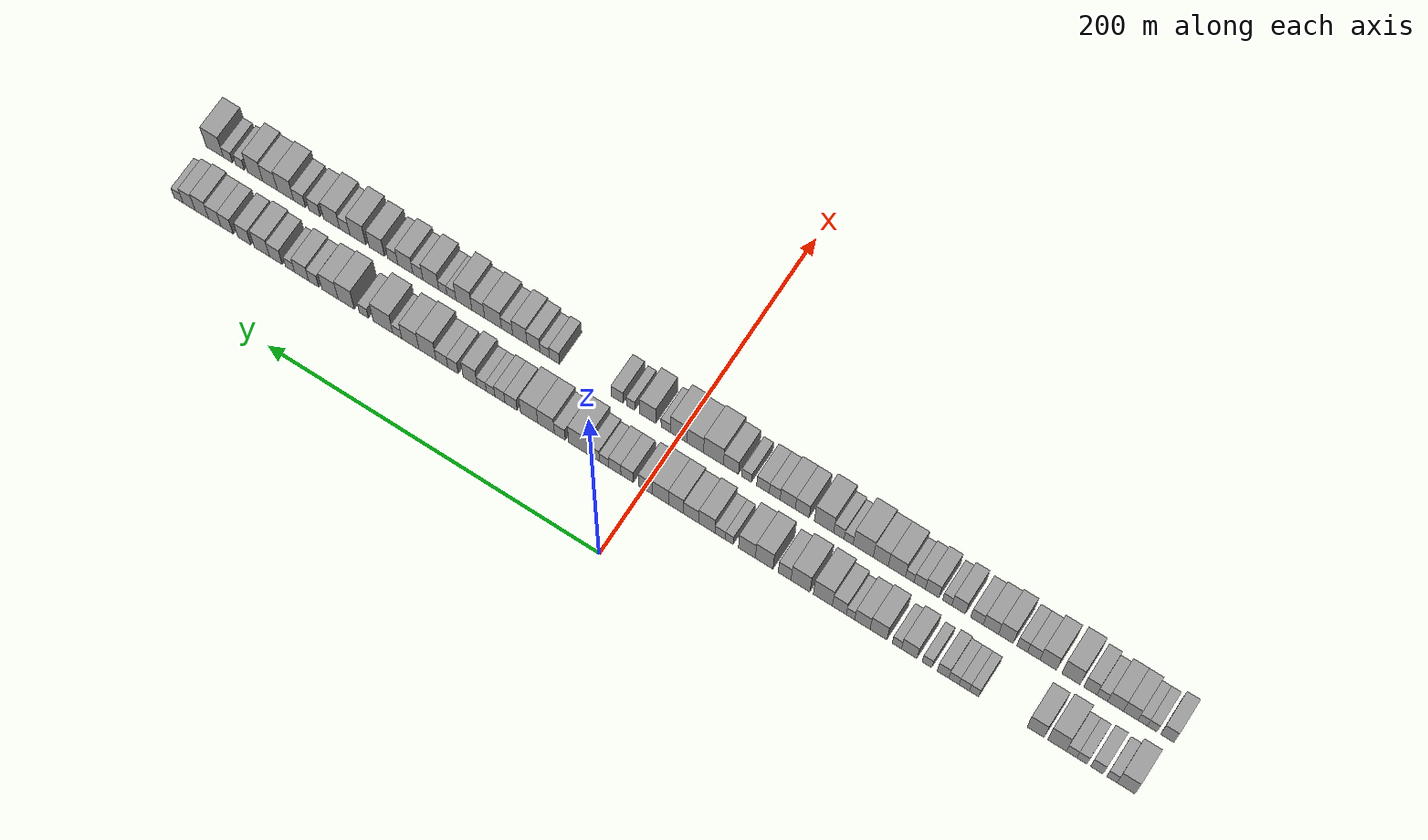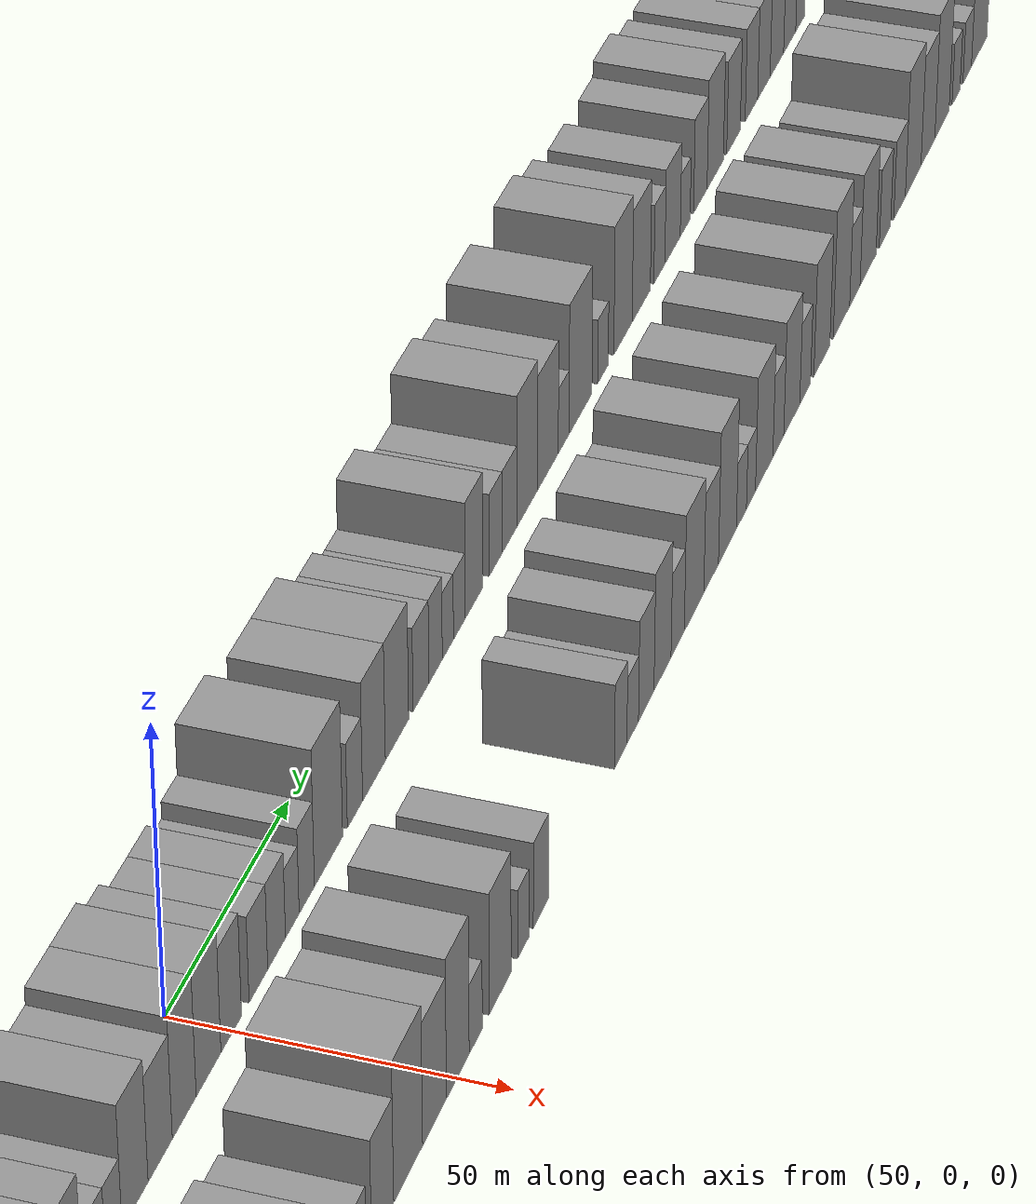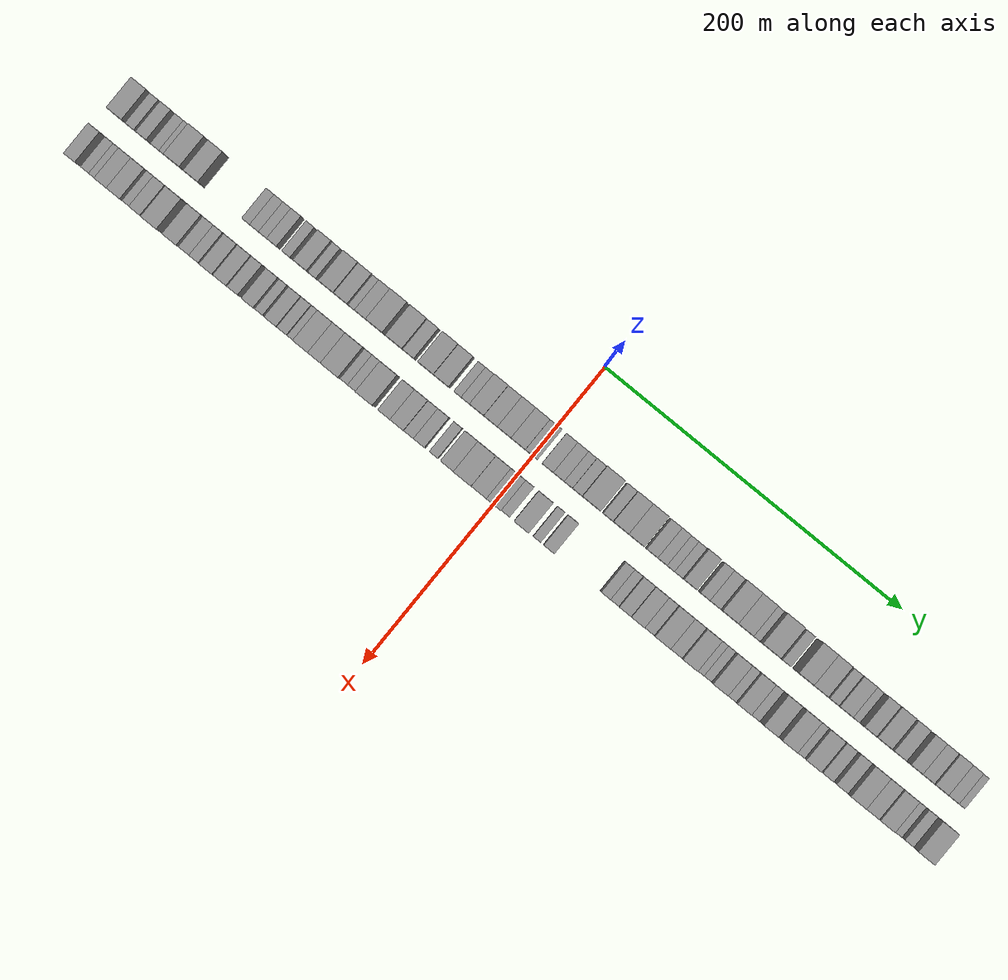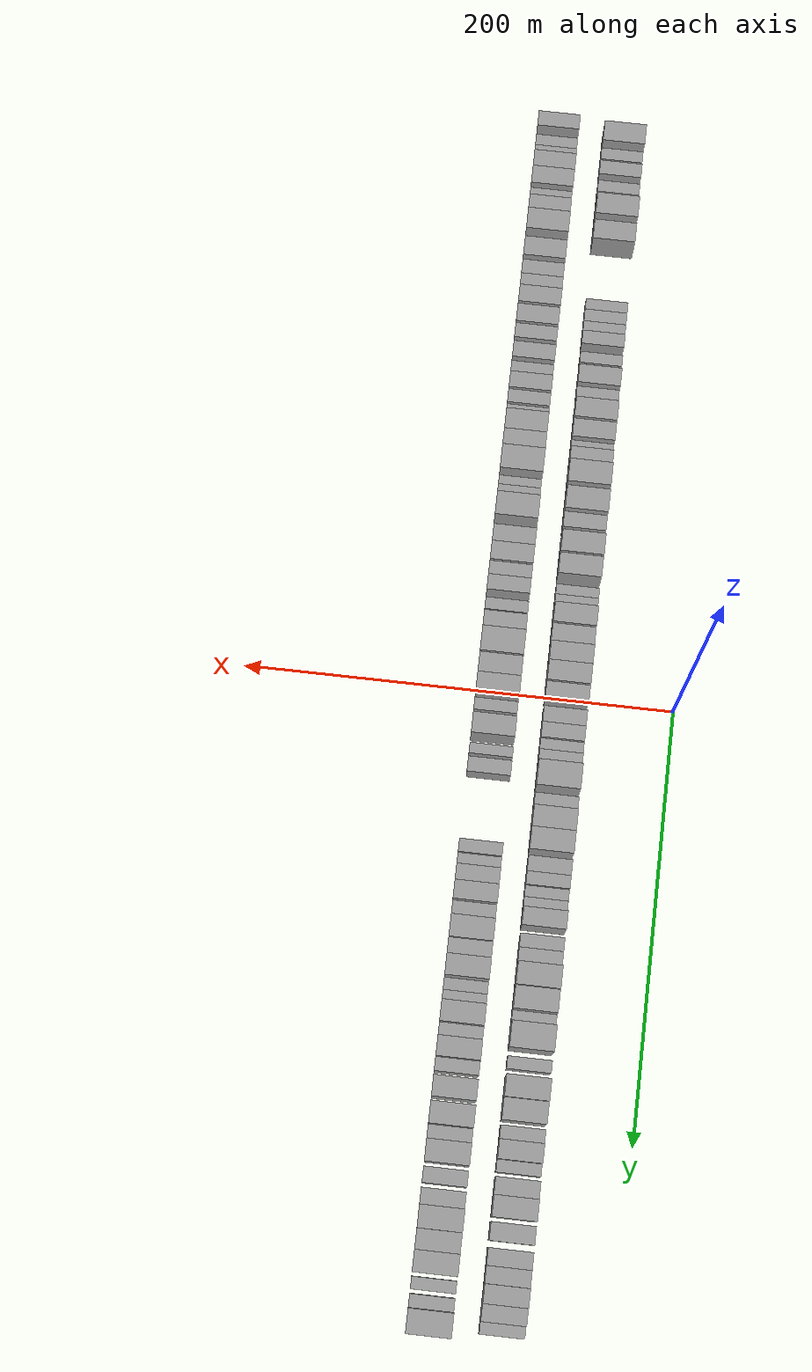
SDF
<sdf version="1.6">
 <world name="default">
  <scene>
   <sky><clouds><speed>12</speed></clouds></sky>
   <ambient>0.4 0.4 0.4 1</ambient>
   <background>0.7 0.7 0.7 1</background>
   <shadows>1</shadows>
  </scene>
  <gravity>0 0 -9.8066</gravity>
  <magnetic_field>6e-06 2.3e-05 -4.2e-05</magnetic_field>
  <physics default="0" name="default_physics" type="ode">
   <ode>
    <solver>
     <type>quick</type>
     <iters>10</iters>
     <sor>1.0</sor>
     <use_dynamic_moi_rescaling>0</use_dynamic_moi_rescaling>
    </solver>
    <constraints>
     <cfm>0</cfm>
     <erp>0.2</erp>
     <contact_max_correcting_vel>100</contact_max_correcting_vel>
     <contact_surface_layer>0.001</contact_surface_layer>
    </constraints>
   </ode>
   <max_step_size>0.004</max_step_size>
   <real_time_factor>1</real_time_factor>
   <real_time_update_rate>250</real_time_update_rate>
  </physics>
  <light name="sun" type="directional">
   <pose>0 0 10 0 0 0</pose>
   <diffuse>0.8 0.8 0.8 1</diffuse>
   <specular>0.2 0.2 0.2 1</specular>
   <attenuation>
    <range>1000</range>
    <constant>0.9</constant>
    <linear>0.01</linear>
    <quadratic>0.001</quadratic>
   </attenuation>
   <direction>-0.5 0.1 -0.9</direction>
  </light>
  <model name="building_1">
   <static>1</static>
   <pose>50.0000 -276.0207 0 0.000000 0.000000 0.000000</pose>
   <link name="link">
    <pose>0 0 10.50 0 0 0</pose>
    <collision name="collision"><geometry><box><size>20.0000 9.9586 21.0000</size></box></geometry></collision>
    <visual name="visual">
     <cast_shadows>0</cast_shadows>
     <geometry><box><size>20.0000 9.9586 21.0000</size></box></geometry>
     <material>
      <script>
       <uri>model://grey_wall/materials/scripts</uri>
       <uri>model://grey_wall/materials/textures</uri>
       <name>vrc/grey_wall</name>
      </script>
     </material>
    </visual>
   </link>
  </model>
  <model name="building_2">
   <static>1</static>
   <pose>50.0000 -268.1680 0 0.000000 0.000000 0.000000</pose>
   <link name="link">
    <pose>0 0 6.00 0 0 0</pose>
    <collision name="collision"><geometry><box><size>20.0000 5.7468 12.0000</size></box></geometry></collision>
    <visual name="visual">
     <cast_shadows>0</cast_shadows>
     <geometry><box><size>20.0000 5.7468 12.0000</size></box></geometry>
     <material>
      <script>
       <uri>model://grey_wall/materials/scripts</uri>
       <uri>model://grey_wall/materials/textures</uri>
       <name>vrc/grey_wall</name>
      </script>
     </material>
    </visual>
   </link>
  </model>
  <model name="building_3">
   <static>1</static>
   <pose>50.0000 -259.8108 0 0.000000 0.000000 0.000000</pose>
   <link name="link">
    <pose>0 0 7.50 0 0 0</pose>
    <collision name="collision"><geometry><box><size>20.0000 6.9677 15.0000</size></box></geometry></collision>
    <visual name="visual">
     <cast_shadows>0</cast_shadows>
     <geometry><box><size>20.0000 6.9677 15.0000</size></box></geometry>
     <material>
      <script>
       <uri>model://grey_wall/materials/scripts</uri>
       <uri>model://grey_wall/materials/textures</uri>
       <name>vrc/grey_wall</name>
      </script>
     </material>
    </visual>
   </link>
  </model>
  <model name="building_4">
   <static>1</static>
   <pose>50.0000 -251.4593 0 0.000000 0.000000 0.000000</pose>
   <link name="link">
    <pose>0 0 6.00 0 0 0</pose>
    <collision name="collision"><geometry><box><size>20.0000 5.7353 12.0000</size></box></geometry></collision>
    <visual name="visual">
     <cast_shadows>0</cast_shadows>
     <geometry><box><size>20.0000 5.7353 12.0000</size></box></geometry>
     <material>
      <script>
       <uri>model://grey_wall/materials/scripts</uri>
       <uri>model://grey_wall/materials/textures</uri>
       <name>vrc/grey_wall</name>
      </script>
     </material>
    </visual>
   </link>
  </model>
  <model name="building_5">
   <static>1</static>
   <pose>50.0000 -245.6844 0 0.000000 0.000000 0.000000</pose>
   <link name="link">
    <pose>0 0 6.00 0 0 0</pose>
    <collision name="collision"><geometry><box><size>20.0000 5.8143 12.0000</size></box></geometry></collision>
    <visual name="visual">
     <cast_shadows>0</cast_shadows>
     <geometry><box><size>20.0000 5.8143 12.0000</size></box></geometry>
     <material>
      <script>
       <uri>model://grey_wall/materials/scripts</uri>
       <uri>model://grey_wall/materials/textures</uri>
       <name>vrc/grey_wall</name>
      </script>
     </material>
    </visual>
   </link>
  </model>
  <model name="building_6">
   <static>1</static>
   <pose>50.0000 -237.5638 0 0.000000 0.000000 0.000000</pose>
   <link name="link">
    <pose>0 0 12.00 0 0 0</pose>
    <collision name="collision"><geometry><box><size>20.0000 10.4269 24.0000</size></box></geometry></collision>
    <visual name="visual">
     <cast_shadows>0</cast_shadows>
     <geometry><box><size>20.0000 10.4269 24.0000</size></box></geometry>
     <material>
      <script>
       <uri>model://grey_wall/materials/scripts</uri>
       <uri>model://grey_wall/materials/textures</uri>
       <name>vrc/grey_wall</name>
      </script>
     </material>
    </visual>
   </link>
  </model>
  <model name="building_7">
   <static>1</static>
   <pose>50.0000 -225.5787 0 0.000000 0.000000 0.000000</pose>
   <link name="link">
    <pose>0 0 10.50 0 0 0</pose>
    <collision name="collision"><geometry><box><size>20.0000 9.5435 21.0000</size></box></geometry></collision>
    <visual name="visual">
     <cast_shadows>0</cast_shadows>
     <geometry><box><size>20.0000 9.5435 21.0000</size></box></geometry>
     <material>
      <script>
       <uri>model://grey_wall/materials/scripts</uri>
       <uri>model://grey_wall/materials/textures</uri>
       <name>vrc/grey_wall</name>
      </script>
     </material>
    </visual>
   </link>
  </model>
  <model name="building_8">
   <static>1</static>
   <pose>50.0000 -190.9284 0 0.000000 0.000000 0.000000</pose>
   <link name="link">
    <pose>0 0 6.00 0 0 0</pose>
    <collision name="collision"><geometry><box><size>20.0000 5.2524 12.0000</size></box></geometry></collision>
    <visual name="visual">
     <cast_shadows>0</cast_shadows>
     <geometry><box><size>20.0000 5.2524 12.0000</size></box></geometry>
     <material>
      <script>
       <uri>model://grey_wall/materials/scripts</uri>
       <uri>model://grey_wall/materials/textures</uri>
       <name>vrc/grey_wall</name>
      </script>
     </material>
    </visual>
   </link>
  </model>
  <model name="building_9">
   <static>1</static>
   <pose>50.0000 -185.3415 0 0.000000 0.000000 0.000000</pose>
   <link name="link">
    <pose>0 0 6.00 0 0 0</pose>
    <collision name="collision"><geometry><box><size>20.0000 5.9213 12.0000</size></box></geometry></collision>
    <visual name="visual">
     <cast_shadows>0</cast_shadows>
     <geometry><box><size>20.0000 5.9213 12.0000</size></box></geometry>
     <material>
      <script>
       <uri>model://grey_wall/materials/scripts</uri>
       <uri>model://grey_wall/materials/textures</uri>
       <name>vrc/grey_wall</name>
      </script>
     </material>
    </visual>
   </link>
  </model>
  <model name="building_10">
   <static>1</static>
   <pose>50.0000 -179.4432 0 0.000000 0.000000 0.000000</pose>
   <link name="link">
    <pose>0 0 6.00 0 0 0</pose>
    <collision name="collision"><geometry><box><size>20.0000 5.8752 12.0000</size></box></geometry></collision>
    <visual name="visual">
     <cast_shadows>0</cast_shadows>
     <geometry><box><size>20.0000 5.8752 12.0000</size></box></geometry>
     <material>
      <script>
       <uri>model://grey_wall/materials/scripts</uri>
       <uri>model://grey_wall/materials/textures</uri>
       <name>vrc/grey_wall</name>
      </script>
     </material>
    </visual>
   </link>
  </model>
  <model name="building_11">
   <static>1</static>
   <pose>50.0000 -173.2333 0 0.000000 0.000000 0.000000</pose>
   <link name="link">
    <pose>0 0 7.50 0 0 0</pose>
    <collision name="collision"><geometry><box><size>20.0000 6.5448 15.0000</size></box></geometry></collision>
    <visual name="visual">
     <cast_shadows>0</cast_shadows>
     <geometry><box><size>20.0000 6.5448 15.0000</size></box></geometry>
     <material>
      <script>
       <uri>model://grey_wall/materials/scripts</uri>
       <uri>model://grey_wall/materials/textures</uri>
       <name>vrc/grey_wall</name>
      </script>
     </material>
    </visual>
   </link>
  </model>
  <model name="building_12">
   <static>1</static>
   <pose>50.0000 -164.2267 0 0.000000 0.000000 0.000000</pose>
   <link name="link">
    <pose>0 0 6.00 0 0 0</pose>
    <collision name="collision"><geometry><box><size>20.0000 5.4684 12.0000</size></box></geometry></collision>
    <visual name="visual">
     <cast_shadows>0</cast_shadows>
     <geometry><box><size>20.0000 5.4684 12.0000</size></box></geometry>
     <material>
      <script>
       <uri>model://grey_wall/materials/scripts</uri>
       <uri>model://grey_wall/materials/textures</uri>
       <name>vrc/grey_wall</name>
      </script>
     </material>
    </visual>
   </link>
  </model>
  <model name="building_13">
   <static>1</static>
   <pose>50.0000 -154.0466 0 0.000000 0.000000 0.000000</pose>
   <link name="link">
    <pose>0 0 9.00 0 0 0</pose>
    <collision name="collision"><geometry><box><size>20.0000 8.8918 18.0000</size></box></geometry></collision>
    <visual name="visual">
     <cast_shadows>0</cast_shadows>
     <geometry><box><size>20.0000 8.8918 18.0000</size></box></geometry>
     <material>
      <script>
       <uri>model://grey_wall/materials/scripts</uri>
       <uri>model://grey_wall/materials/textures</uri>
       <name>vrc/grey_wall</name>
      </script>
     </material>
    </visual>
   </link>
  </model>
  <model name="building_14">
   <static>1</static>
   <pose>50.0000 -146.9675 0 0.000000 0.000000 0.000000</pose>
   <link name="link">
    <pose>0 0 6.00 0 0 0</pose>
    <collision name="collision"><geometry><box><size>20.0000 5.2665 12.0000</size></box></geometry></collision>
    <visual name="visual">
     <cast_shadows>0</cast_shadows>
     <geometry><box><size>20.0000 5.2665 12.0000</size></box></geometry>
     <material>
      <script>
       <uri>model://grey_wall/materials/scripts</uri>
       <uri>model://grey_wall/materials/textures</uri>
       <name>vrc/grey_wall</name>
      </script>
     </material>
    </visual>
   </link>
  </model>
  <model name="building_15">
   <static>1</static>
   <pose>50.0000 -136.4984 0 0.000000 0.000000 0.000000</pose>
   <link name="link">
    <pose>0 0 10.50 0 0 0</pose>
    <collision name="collision"><geometry><box><size>20.0000 9.6715 21.0000</size></box></geometry></collision>
    <visual name="visual">
     <cast_shadows>0</cast_shadows>
     <geometry><box><size>20.0000 9.6715 21.0000</size></box></geometry>
     <material>
      <script>
       <uri>model://grey_wall/materials/scripts</uri>
       <uri>model://grey_wall/materials/textures</uri>
       <name>vrc/grey_wall</name>
      </script>
     </material>
    </visual>
   </link>
  </model>
  <model name="building_16">
   <static>1</static>
   <pose>50.0000 -127.2454 0 0.000000 0.000000 0.000000</pose>
   <link name="link">
    <pose>0 0 9.00 0 0 0</pose>
    <collision name="collision"><geometry><box><size>20.0000 8.8345 18.0000</size></box></geometry></collision>
    <visual name="visual">
     <cast_shadows>0</cast_shadows>
     <geometry><box><size>20.0000 8.8345 18.0000</size></box></geometry>
     <material>
      <script>
       <uri>model://grey_wall/materials/scripts</uri>
       <uri>model://grey_wall/materials/textures</uri>
       <name>vrc/grey_wall</name>
      </script>
     </material>
    </visual>
   </link>
  </model>
  <model name="building_17">
   <static>1</static>
   <pose>50.0000 -120.4018 0 0.000000 0.000000 0.000000</pose>
   <link name="link">
    <pose>0 0 6.00 0 0 0</pose>
    <collision name="collision"><geometry><box><size>20.0000 4.8527 12.0000</size></box></geometry></collision>
    <visual name="visual">
     <cast_shadows>0</cast_shadows>
     <geometry><box><size>20.0000 4.8527 12.0000</size></box></geometry>
     <material>
      <script>
       <uri>model://grey_wall/materials/scripts</uri>
       <uri>model://grey_wall/materials/textures</uri>
       <name>vrc/grey_wall</name>
      </script>
     </material>
    </visual>
   </link>
  </model>
  <model name="building_18">
   <static>1</static>
   <pose>50.0000 -113.9878 0 0.000000 0.000000 0.000000</pose>
   <link name="link">
    <pose>0 0 9.00 0 0 0</pose>
    <collision name="collision"><geometry><box><size>20.0000 7.9753 18.0000</size></box></geometry></collision>
    <visual name="visual">
     <cast_shadows>0</cast_shadows>
     <geometry><box><size>20.0000 7.9753 18.0000</size></box></geometry>
     <material>
      <script>
       <uri>model://grey_wall/materials/scripts</uri>
       <uri>model://grey_wall/materials/textures</uri>
       <name>vrc/grey_wall</name>
      </script>
     </material>
    </visual>
   </link>
  </model>
  <model name="building_19">
   <static>1</static>
   <pose>50.0000 -104.5113 0 0.000000 0.000000 0.000000</pose>
   <link name="link">
    <pose>0 0 12.00 0 0 0</pose>
    <collision name="collision"><geometry><box><size>20.0000 10.9776 24.0000</size></box></geometry></collision>
    <visual name="visual">
     <cast_shadows>0</cast_shadows>
     <geometry><box><size>20.0000 10.9776 24.0000</size></box></geometry>
     <material>
      <script>
       <uri>model://grey_wall/materials/scripts</uri>
       <uri>model://grey_wall/materials/textures</uri>
       <name>vrc/grey_wall</name>
      </script>
     </material>
    </visual>
   </link>
  </model>
  <model name="building_20">
   <static>1</static>
   <pose>50.0000 -91.5438 0 0.000000 0.000000 0.000000</pose>
   <link name="link">
    <pose>0 0 12.00 0 0 0</pose>
    <collision name="collision"><geometry><box><size>20.0000 10.9575 24.0000</size></box></geometry></collision>
    <visual name="visual">
     <cast_shadows>0</cast_shadows>
     <geometry><box><size>20.0000 10.9575 24.0000</size></box></geometry>
     <material>
      <script>
       <uri>model://grey_wall/materials/scripts</uri>
       <uri>model://grey_wall/materials/textures</uri>
       <name>vrc/grey_wall</name>
      </script>
     </material>
    </visual>
   </link>
  </model>
  <model name="building_21">
   <static>1</static>
   <pose>50.0000 -82.3586 0 0.000000 0.000000 0.000000</pose>
   <link name="link">
    <pose>0 0 9.00 0 0 0</pose>
    <collision name="collision"><geometry><box><size>20.0000 7.4127 18.0000</size></box></geometry></collision>
    <visual name="visual">
     <cast_shadows>0</cast_shadows>
     <geometry><box><size>20.0000 7.4127 18.0000</size></box></geometry>
     <material>
      <script>
       <uri>model://grey_wall/materials/scripts</uri>
       <uri>model://grey_wall/materials/textures</uri>
       <name>vrc/grey_wall</name>
      </script>
     </material>
    </visual>
   </link>
  </model>
  <model name="building_22">
   <static>1</static>
   <pose>50.0000 -70.5201 0 0.000000 0.000000 0.000000</pose>
   <link name="link">
    <pose>0 0 12.00 0 0 0</pose>
    <collision name="collision"><geometry><box><size>20.0000 10.2644 24.0000</size></box></geometry></collision>
    <visual name="visual">
     <cast_shadows>0</cast_shadows>
     <geometry><box><size>20.0000 10.2644 24.0000</size></box></geometry>
     <material>
      <script>
       <uri>model://grey_wall/materials/scripts</uri>
       <uri>model://grey_wall/materials/textures</uri>
       <name>vrc/grey_wall</name>
      </script>
     </material>
    </visual>
   </link>
  </model>
  <model name="building_23">
   <static>1</static>
   <pose>50.0000 -60.4606 0 0.000000 0.000000 0.000000</pose>
   <link name="link">
    <pose>0 0 10.50 0 0 0</pose>
    <collision name="collision"><geometry><box><size>20.0000 9.8546 21.0000</size></box></geometry></collision>
    <visual name="visual">
     <cast_shadows>0</cast_shadows>
     <geometry><box><size>20.0000 9.8546 21.0000</size></box></geometry>
     <material>
      <script>
       <uri>model://grey_wall/materials/scripts</uri>
       <uri>model://grey_wall/materials/textures</uri>
       <name>vrc/grey_wall</name>
      </script>
     </material>
    </visual>
   </link>
  </model>
  <model name="building_24">
   <static>1</static>
   <pose>50.0000 -50.1069 0 0.000000 0.000000 0.000000</pose>
   <link name="link">
    <pose>0 0 6.00 0 0 0</pose>
    <collision name="collision"><geometry><box><size>20.0000 4.8529 12.0000</size></box></geometry></collision>
    <visual name="visual">
     <cast_shadows>0</cast_shadows>
     <geometry><box><size>20.0000 4.8529 12.0000</size></box></geometry>
     <material>
      <script>
       <uri>model://grey_wall/materials/scripts</uri>
       <uri>model://grey_wall/materials/textures</uri>
       <name>vrc/grey_wall</name>
      </script>
     </material>
    </visual>
   </link>
  </model>
  <model name="building_25">
   <static>1</static>
   <pose>50.0000 -44.7329 0 0.000000 0.000000 0.000000</pose>
   <link name="link">
    <pose>0 0 6.00 0 0 0</pose>
    <collision name="collision"><geometry><box><size>20.0000 5.8950 12.0000</size></box></geometry></collision>
    <visual name="visual">
     <cast_shadows>0</cast_shadows>
     <geometry><box><size>20.0000 5.8950 12.0000</size></box></geometry>
     <material>
      <script>
       <uri>model://grey_wall/materials/scripts</uri>
       <uri>model://grey_wall/materials/textures</uri>
       <name>vrc/grey_wall</name>
      </script>
     </material>
    </visual>
   </link>
  </model>
  <model name="building_26">
   <static>1</static>
   <pose>50.0000 -37.0605 0 0.000000 0.000000 0.000000</pose>
   <link name="link">
    <pose>0 0 10.50 0 0 0</pose>
    <collision name="collision"><geometry><box><size>20.0000 9.4498 21.0000</size></box></geometry></collision>
    <visual name="visual">
     <cast_shadows>0</cast_shadows>
     <geometry><box><size>20.0000 9.4498 21.0000</size></box></geometry>
     <material>
      <script>
       <uri>model://grey_wall/materials/scripts</uri>
       <uri>model://grey_wall/materials/textures</uri>
       <name>vrc/grey_wall</name>
      </script>
     </material>
    </visual>
   </link>
  </model>
  <model name="building_27">
   <static>1</static>
   <pose>50.0000 -27.8437 0 0.000000 0.000000 0.000000</pose>
   <link name="link">
    <pose>0 0 9.00 0 0 0</pose>
    <collision name="collision"><geometry><box><size>20.0000 8.9838 18.0000</size></box></geometry></collision>
    <visual name="visual">
     <cast_shadows>0</cast_shadows>
     <geometry><box><size>20.0000 8.9838 18.0000</size></box></geometry>
     <material>
      <script>
       <uri>model://grey_wall/materials/scripts</uri>
       <uri>model://grey_wall/materials/textures</uri>
       <name>vrc/grey_wall</name>
      </script>
     </material>
    </visual>
   </link>
  </model>
  <model name="building_28">
   <static>1</static>
   <pose>50.0000 -18.8576 0 0.000000 0.000000 0.000000</pose>
   <link name="link">
    <pose>0 0 10.50 0 0 0</pose>
    <collision name="collision"><geometry><box><size>20.0000 8.9882 21.0000</size></box></geometry></collision>
    <visual name="visual">
     <cast_shadows>0</cast_shadows>
     <geometry><box><size>20.0000 8.9882 21.0000</size></box></geometry>
     <material>
      <script>
       <uri>model://grey_wall/materials/scripts</uri>
       <uri>model://grey_wall/materials/textures</uri>
       <name>vrc/grey_wall</name>
      </script>
     </material>
    </visual>
   </link>
  </model>
  <model name="building_29">
   <static>1</static>
   <pose>50.0000 -9.6039 0 0.000000 0.000000 0.000000</pose>
   <link name="link">
    <pose>0 0 10.50 0 0 0</pose>
    <collision name="collision"><geometry><box><size>20.0000 9.5193 21.0000</size></box></geometry></collision>
    <visual name="visual">
     <cast_shadows>0</cast_shadows>
     <geometry><box><size>20.0000 9.5193 21.0000</size></box></geometry>
     <material>
      <script>
       <uri>model://grey_wall/materials/scripts</uri>
       <uri>model://grey_wall/materials/textures</uri>
       <name>vrc/grey_wall</name>
      </script>
     </material>
    </visual>
   </link>
  </model>
  <model name="building_30">
   <static>1</static>
   <pose>50.0000 -0.8209 0 0.000000 0.000000 0.000000</pose>
   <link name="link">
    <pose>0 0 9.00 0 0 0</pose>
    <collision name="collision"><geometry><box><size>20.0000 8.0467 18.0000</size></box></geometry></collision>
    <visual name="visual">
     <cast_shadows>0</cast_shadows>
     <geometry><box><size>20.0000 8.0467 18.0000</size></box></geometry>
     <material>
      <script>
       <uri>model://grey_wall/materials/scripts</uri>
       <uri>model://grey_wall/materials/textures</uri>
       <name>vrc/grey_wall</name>
      </script>
     </material>
    </visual>
   </link>
  </model>
  <model name="building_31">
   <static>1</static>
   <pose>50.0000 9.9251 0 0.000000 0.000000 0.000000</pose>
   <link name="link">
    <pose>0 0 7.50 0 0 0</pose>
    <collision name="collision"><geometry><box><size>20.0000 7.4453 15.0000</size></box></geometry></collision>
    <visual name="visual">
     <cast_shadows>0</cast_shadows>
     <geometry><box><size>20.0000 7.4453 15.0000</size></box></geometry>
     <material>
      <script>
       <uri>model://grey_wall/materials/scripts</uri>
       <uri>model://grey_wall/materials/textures</uri>
       <name>vrc/grey_wall</name>
      </script>
     </material>
    </visual>
   </link>
  </model>
  <model name="building_32">
   <static>1</static>
   <pose>50.0000 17.2544 0 0.000000 0.000000 0.000000</pose>
   <link name="link">
    <pose>0 0 7.50 0 0 0</pose>
    <collision name="collision"><geometry><box><size>20.0000 7.2133 15.0000</size></box></geometry></collision>
    <visual name="visual">
     <cast_shadows>0</cast_shadows>
     <geometry><box><size>20.0000 7.2133 15.0000</size></box></geometry>
     <material>
      <script>
       <uri>model://grey_wall/materials/scripts</uri>
       <uri>model://grey_wall/materials/textures</uri>
       <name>vrc/grey_wall</name>
      </script>
     </material>
    </visual>
   </link>
  </model>
  <model name="building_33">
   <static>1</static>
   <pose>50.0000 23.6577 0 0.000000 0.000000 0.000000</pose>
   <link name="link">
    <pose>0 0 6.00 0 0 0</pose>
    <collision name="collision"><geometry><box><size>20.0000 5.5933 12.0000</size></box></geometry></collision>
    <visual name="visual">
     <cast_shadows>0</cast_shadows>
     <geometry><box><size>20.0000 5.5933 12.0000</size></box></geometry>
     <material>
      <script>
       <uri>model://grey_wall/materials/scripts</uri>
       <uri>model://grey_wall/materials/textures</uri>
       <name>vrc/grey_wall</name>
      </script>
     </material>
    </visual>
   </link>
  </model>
  <model name="building_34">
   <static>1</static>
   <pose>50.0000 29.6314 0 0.000000 0.000000 0.000000</pose>
   <link name="link">
    <pose>0 0 7.50 0 0 0</pose>
    <collision name="collision"><geometry><box><size>20.0000 6.3542 15.0000</size></box></geometry></collision>
    <visual name="visual">
     <cast_shadows>0</cast_shadows>
     <geometry><box><size>20.0000 6.3542 15.0000</size></box></geometry>
     <material>
      <script>
       <uri>model://grey_wall/materials/scripts</uri>
       <uri>model://grey_wall/materials/textures</uri>
       <name>vrc/grey_wall</name>
      </script>
     </material>
    </visual>
   </link>
  </model>
  <model name="building_35">
   <static>1</static>
   <pose>50.0000 38.7685 0 0.000000 0.000000 0.000000</pose>
   <link name="link">
    <pose>0 0 12.00 0 0 0</pose>
    <collision name="collision"><geometry><box><size>20.0000 11.9199 24.0000</size></box></geometry></collision>
    <visual name="visual">
     <cast_shadows>0</cast_shadows>
     <geometry><box><size>20.0000 11.9199 24.0000</size></box></geometry>
     <material>
      <script>
       <uri>model://grey_wall/materials/scripts</uri>
       <uri>model://grey_wall/materials/textures</uri>
       <name>vrc/grey_wall</name>
      </script>
     </material>
    </visual>
   </link>
  </model>
  <model name="building_36">
   <static>1</static>
   <pose>50.0000 50.0212 0 0.000000 0.000000 0.000000</pose>
   <link name="link">
    <pose>0 0 7.50 0 0 0</pose>
    <collision name="collision"><geometry><box><size>20.0000 6.5854 15.0000</size></box></geometry></collision>
    <visual name="visual">
     <cast_shadows>0</cast_shadows>
     <geometry><box><size>20.0000 6.5854 15.0000</size></box></geometry>
     <material>
      <script>
       <uri>model://grey_wall/materials/scripts</uri>
       <uri>model://grey_wall/materials/textures</uri>
       <name>vrc/grey_wall</name>
      </script>
     </material>
    </visual>
   </link>
  </model>
  <model name="building_37">
   <static>1</static>
   <pose>50.0000 58.3000 0 0.000000 0.000000 0.000000</pose>
   <link name="link">
    <pose>0 0 10.50 0 0 0</pose>
    <collision name="collision"><geometry><box><size>20.0000 9.9722 21.0000</size></box></geometry></collision>
    <visual name="visual">
     <cast_shadows>0</cast_shadows>
     <geometry><box><size>20.0000 9.9722 21.0000</size></box></geometry>
     <material>
      <script>
       <uri>model://grey_wall/materials/scripts</uri>
       <uri>model://grey_wall/materials/textures</uri>
       <name>vrc/grey_wall</name>
      </script>
     </material>
    </visual>
   </link>
  </model>
  <model name="building_38">
   <static>1</static>
   <pose>50.0000 68.4971 0 0.000000 0.000000 0.000000</pose>
   <link name="link">
    <pose>0 0 10.50 0 0 0</pose>
    <collision name="collision"><geometry><box><size>20.0000 10.4220 21.0000</size></box></geometry></collision>
    <visual name="visual">
     <cast_shadows>0</cast_shadows>
     <geometry><box><size>20.0000 10.4220 21.0000</size></box></geometry>
     <material>
      <script>
       <uri>model://grey_wall/materials/scripts</uri>
       <uri>model://grey_wall/materials/textures</uri>
       <name>vrc/grey_wall</name>
      </script>
     </material>
    </visual>
   </link>
  </model>
  <model name="building_39">
   <static>1</static>
   <pose>50.0000 79.3387 0 0.000000 0.000000 0.000000</pose>
   <link name="link">
    <pose>0 0 7.50 0 0 0</pose>
    <collision name="collision"><geometry><box><size>20.0000 7.2612 15.0000</size></box></geometry></collision>
    <visual name="visual">
     <cast_shadows>0</cast_shadows>
     <geometry><box><size>20.0000 7.2612 15.0000</size></box></geometry>
     <material>
      <script>
       <uri>model://grey_wall/materials/scripts</uri>
       <uri>model://grey_wall/materials/textures</uri>
       <name>vrc/grey_wall</name>
      </script>
     </material>
    </visual>
   </link>
  </model>
  <model name="building_40">
   <static>1</static>
   <pose>50.0000 86.0301 0 0.000000 0.000000 0.000000</pose>
   <link name="link">
    <pose>0 0 7.50 0 0 0</pose>
    <collision name="collision"><geometry><box><size>20.0000 6.1216 15.0000</size></box></geometry></collision>
    <visual name="visual">
     <cast_shadows>0</cast_shadows>
     <geometry><box><size>20.0000 6.1216 15.0000</size></box></geometry>
     <material>
      <script>
       <uri>model://grey_wall/materials/scripts</uri>
       <uri>model://grey_wall/materials/textures</uri>
       <name>vrc/grey_wall</name>
      </script>
     </material>
    </visual>
   </link>
  </model>
  <model name="building_41">
   <static>1</static>
   <pose>50.0000 91.6999 0 0.000000 0.000000 0.000000</pose>
   <link name="link">
    <pose>0 0 6.00 0 0 0</pose>
    <collision name="collision"><geometry><box><size>20.0000 5.2180 12.0000</size></box></geometry></collision>
    <visual name="visual">
     <cast_shadows>0</cast_shadows>
     <geometry><box><size>20.0000 5.2180 12.0000</size></box></geometry>
     <material>
      <script>
       <uri>model://grey_wall/materials/scripts</uri>
       <uri>model://grey_wall/materials/textures</uri>
       <name>vrc/grey_wall</name>
      </script>
     </material>
    </visual>
   </link>
  </model>
  <model name="building_42">
   <static>1</static>
   <pose>50.0000 97.0927 0 0.000000 0.000000 0.000000</pose>
   <link name="link">
    <pose>0 0 6.00 0 0 0</pose>
    <collision name="collision"><geometry><box><size>20.0000 5.5674 12.0000</size></box></geometry></collision>
    <visual name="visual">
     <cast_shadows>0</cast_shadows>
     <geometry><box><size>20.0000 5.5674 12.0000</size></box></geometry>
     <material>
      <script>
       <uri>model://grey_wall/materials/scripts</uri>
       <uri>model://grey_wall/materials/textures</uri>
       <name>vrc/grey_wall</name>
      </script>
     </material>
    </visual>
   </link>
  </model>
  <model name="building_43">
   <static>1</static>
   <pose>50.0000 104.0828 0 0.000000 0.000000 0.000000</pose>
   <link name="link">
    <pose>0 0 10.50 0 0 0</pose>
    <collision name="collision"><geometry><box><size>20.0000 8.4127 21.0000</size></box></geometry></collision>
    <visual name="visual">
     <cast_shadows>0</cast_shadows>
     <geometry><box><size>20.0000 8.4127 21.0000</size></box></geometry>
     <material>
      <script>
       <uri>model://grey_wall/materials/scripts</uri>
       <uri>model://grey_wall/materials/textures</uri>
       <name>vrc/grey_wall</name>
      </script>
     </material>
    </visual>
   </link>
  </model>
  <model name="building_44">
   <static>1</static>
   <pose>50.0000 114.4415 0 0.000000 0.000000 0.000000</pose>
   <link name="link">
    <pose>0 0 7.50 0 0 0</pose>
    <collision name="collision"><geometry><box><size>20.0000 6.3048 15.0000</size></box></geometry></collision>
    <visual name="visual">
     <cast_shadows>0</cast_shadows>
     <geometry><box><size>20.0000 6.3048 15.0000</size></box></geometry>
     <material>
      <script>
       <uri>model://grey_wall/materials/scripts</uri>
       <uri>model://grey_wall/materials/textures</uri>
       <name>vrc/grey_wall</name>
      </script>
     </material>
    </visual>
   </link>
  </model>
  <model name="building_45">
   <static>1</static>
   <pose>50.0000 121.1762 0 0.000000 0.000000 0.000000</pose>
   <link name="link">
    <pose>0 0 7.50 0 0 0</pose>
    <collision name="collision"><geometry><box><size>20.0000 7.1645 15.0000</size></box></geometry></collision>
    <visual name="visual">
     <cast_shadows>0</cast_shadows>
     <geometry><box><size>20.0000 7.1645 15.0000</size></box></geometry>
     <material>
      <script>
       <uri>model://grey_wall/materials/scripts</uri>
       <uri>model://grey_wall/materials/textures</uri>
       <name>vrc/grey_wall</name>
      </script>
     </material>
    </visual>
   </link>
  </model>
  <model name="building_46">
   <static>1</static>
   <pose>50.0000 129.9872 0 0.000000 0.000000 0.000000</pose>
   <link name="link">
    <pose>0 0 12.00 0 0 0</pose>
    <collision name="collision"><geometry><box><size>20.0000 10.4575 24.0000</size></box></geometry></collision>
    <visual name="visual">
     <cast_shadows>0</cast_shadows>
     <geometry><box><size>20.0000 10.4575 24.0000</size></box></geometry>
     <material>
      <script>
       <uri>model://grey_wall/materials/scripts</uri>
       <uri>model://grey_wall/materials/textures</uri>
       <name>vrc/grey_wall</name>
      </script>
     </material>
    </visual>
   </link>
  </model>
  <model name="building_47">
   <static>1</static>
   <pose>50.0000 140.4449 0 0.000000 0.000000 0.000000</pose>
   <link name="link">
    <pose>0 0 10.50 0 0 0</pose>
    <collision name="collision"><geometry><box><size>20.0000 10.4578 21.0000</size></box></geometry></collision>
    <visual name="visual">
     <cast_shadows>0</cast_shadows>
     <geometry><box><size>20.0000 10.4578 21.0000</size></box></geometry>
     <material>
      <script>
       <uri>model://grey_wall/materials/scripts</uri>
       <uri>model://grey_wall/materials/textures</uri>
       <name>vrc/grey_wall</name>
      </script>
     </material>
    </visual>
   </link>
  </model>
  <model name="building_48">
   <static>1</static>
   <pose>50.0000 148.4528 0 0.000000 0.000000 0.000000</pose>
   <link name="link">
    <pose>0 0 6.00 0 0 0</pose>
    <collision name="collision"><geometry><box><size>20.0000 5.5581 12.0000</size></box></geometry></collision>
    <visual name="visual">
     <cast_shadows>0</cast_shadows>
     <geometry><box><size>20.0000 5.5581 12.0000</size></box></geometry>
     <material>
      <script>
       <uri>model://grey_wall/materials/scripts</uri>
       <uri>model://grey_wall/materials/textures</uri>
       <name>vrc/grey_wall</name>
      </script>
     </material>
    </visual>
   </link>
  </model>
  <model name="building_49">
   <static>1</static>
   <pose>50.0000 157.2001 0 0.000000 0.000000 0.000000</pose>
   <link name="link">
    <pose>0 0 12.00 0 0 0</pose>
    <collision name="collision"><geometry><box><size>20.0000 11.9365 24.0000</size></box></geometry></collision>
    <visual name="visual">
     <cast_shadows>0</cast_shadows>
     <geometry><box><size>20.0000 11.9365 24.0000</size></box></geometry>
     <material>
      <script>
       <uri>model://grey_wall/materials/scripts</uri>
       <uri>model://grey_wall/materials/textures</uri>
       <name>vrc/grey_wall</name>
      </script>
     </material>
    </visual>
   </link>
  </model>
  <model name="building_50">
   <static>1</static>
   <pose>50.0000 169.0229 0 0.000000 0.000000 0.000000</pose>
   <link name="link">
    <pose>0 0 6.00 0 0 0</pose>
    <collision name="collision"><geometry><box><size>20.0000 5.7092 12.0000</size></box></geometry></collision>
    <visual name="visual">
     <cast_shadows>0</cast_shadows>
     <geometry><box><size>20.0000 5.7092 12.0000</size></box></geometry>
     <material>
      <script>
       <uri>model://grey_wall/materials/scripts</uri>
       <uri>model://grey_wall/materials/textures</uri>
       <name>vrc/grey_wall</name>
      </script>
     </material>
    </visual>
   </link>
  </model>
  <model name="building_51">
   <static>1</static>
   <pose>50.0000 179.8717 0 0.000000 0.000000 0.000000</pose>
   <link name="link">
    <pose>0 0 12.00 0 0 0</pose>
    <collision name="collision"><geometry><box><size>20.0000 9.9882 24.0000</size></box></geometry></collision>
    <visual name="visual">
     <cast_shadows>0</cast_shadows>
     <geometry><box><size>20.0000 9.9882 24.0000</size></box></geometry>
     <material>
      <script>
       <uri>model://grey_wall/materials/scripts</uri>
       <uri>model://grey_wall/materials/textures</uri>
       <name>vrc/grey_wall</name>
      </script>
     </material>
    </visual>
   </link>
  </model>
  <model name="building_52">
   <static>1</static>
   <pose>50.0000 189.8751 0 0.000000 0.000000 0.000000</pose>
   <link name="link">
    <pose>0 0 10.50 0 0 0</pose>
    <collision name="collision"><geometry><box><size>20.0000 10.0186 21.0000</size></box></geometry></collision>
    <visual name="visual">
     <cast_shadows>0</cast_shadows>
     <geometry><box><size>20.0000 10.0186 21.0000</size></box></geometry>
     <material>
      <script>
       <uri>model://grey_wall/materials/scripts</uri>
       <uri>model://grey_wall/materials/textures</uri>
       <name>vrc/grey_wall</name>
      </script>
     </material>
    </visual>
   </link>
  </model>
  <model name="building_53">
   <static>1</static>
   <pose>50.0000 199.9680 0 0.000000 0.000000 0.000000</pose>
   <link name="link">
    <pose>0 0 7.50 0 0 0</pose>
    <collision name="collision"><geometry><box><size>20.0000 6.1673 15.0000</size></box></geometry></collision>
    <visual name="visual">
     <cast_shadows>0</cast_shadows>
     <geometry><box><size>20.0000 6.1673 15.0000</size></box></geometry>
     <material>
      <script>
       <uri>model://grey_wall/materials/scripts</uri>
       <uri>model://grey_wall/materials/textures</uri>
       <name>vrc/grey_wall</name>
      </script>
     </material>
    </visual>
   </link>
  </model>
  <model name="building_54">
   <static>1</static>
   <pose>50.0000 207.4284 0 0.000000 0.000000 0.000000</pose>
   <link name="link">
    <pose>0 0 9.00 0 0 0</pose>
    <collision name="collision"><geometry><box><size>20.0000 8.7535 18.0000</size></box></geometry></collision>
    <visual name="visual">
     <cast_shadows>0</cast_shadows>
     <geometry><box><size>20.0000 8.7535 18.0000</size></box></geometry>
     <material>
      <script>
       <uri>model://grey_wall/materials/scripts</uri>
       <uri>model://grey_wall/materials/textures</uri>
       <name>vrc/grey_wall</name>
      </script>
     </material>
    </visual>
   </link>
  </model>
  <model name="building_55">
   <static>1</static>
   <pose>50.0000 214.6460 0 0.000000 0.000000 0.000000</pose>
   <link name="link">
    <pose>0 0 6.00 0 0 0</pose>
    <collision name="collision"><geometry><box><size>20.0000 5.6817 12.0000</size></box></geometry></collision>
    <visual name="visual">
     <cast_shadows>0</cast_shadows>
     <geometry><box><size>20.0000 5.6817 12.0000</size></box></geometry>
     <material>
      <script>
       <uri>model://grey_wall/materials/scripts</uri>
       <uri>model://grey_wall/materials/textures</uri>
       <name>vrc/grey_wall</name>
      </script>
     </material>
    </visual>
   </link>
  </model>
  <model name="building_56">
   <static>1</static>
   <pose>50.0000 223.4304 0 0.000000 0.000000 0.000000</pose>
   <link name="link">
    <pose>0 0 9.00 0 0 0</pose>
    <collision name="collision"><geometry><box><size>20.0000 7.8871 18.0000</size></box></geometry></collision>
    <visual name="visual">
     <cast_shadows>0</cast_shadows>
     <geometry><box><size>20.0000 7.8871 18.0000</size></box></geometry>
     <material>
      <script>
       <uri>model://grey_wall/materials/scripts</uri>
       <uri>model://grey_wall/materials/textures</uri>
       <name>vrc/grey_wall</name>
      </script>
     </material>
    </visual>
   </link>
  </model>
  <model name="building_57">
   <static>1</static>
   <pose>50.0000 232.1941 0 0.000000 0.000000 0.000000</pose>
   <link name="link">
    <pose>0 0 10.50 0 0 0</pose>
    <collision name="collision"><geometry><box><size>20.0000 9.6404 21.0000</size></box></geometry></collision>
    <visual name="visual">
     <cast_shadows>0</cast_shadows>
     <geometry><box><size>20.0000 9.6404 21.0000</size></box></geometry>
     <material>
      <script>
       <uri>model://grey_wall/materials/scripts</uri>
       <uri>model://grey_wall/materials/textures</uri>
       <name>vrc/grey_wall</name>
      </script>
     </material>
    </visual>
   </link>
  </model>
  <model name="building_58">
   <static>1</static>
   <pose>50.0000 243.1119 0 0.000000 0.000000 0.000000</pose>
   <link name="link">
    <pose>0 0 9.00 0 0 0</pose>
    <collision name="collision"><geometry><box><size>20.0000 8.1951 18.0000</size></box></geometry></collision>
    <visual name="visual">
     <cast_shadows>0</cast_shadows>
     <geometry><box><size>20.0000 8.1951 18.0000</size></box></geometry>
     <material>
      <script>
       <uri>model://grey_wall/materials/scripts</uri>
       <uri>model://grey_wall/materials/textures</uri>
       <name>vrc/grey_wall</name>
      </script>
     </material>
    </visual>
   </link>
  </model>
  <model name="building_59">
   <static>1</static>
   <pose>50.0000 254.0424 0 0.000000 0.000000 0.000000</pose>
   <link name="link">
    <pose>0 0 9.00 0 0 0</pose>
    <collision name="collision"><geometry><box><size>20.0000 7.6658 18.0000</size></box></geometry></collision>
    <visual name="visual">
     <cast_shadows>0</cast_shadows>
     <geometry><box><size>20.0000 7.6658 18.0000</size></box></geometry>
     <material>
      <script>
       <uri>model://grey_wall/materials/scripts</uri>
       <uri>model://grey_wall/materials/textures</uri>
       <name>vrc/grey_wall</name>
      </script>
     </material>
    </visual>
   </link>
  </model>
  <model name="building_60">
   <static>1</static>
   <pose>50.0000 261.7490 0 0.000000 0.000000 0.000000</pose>
   <link name="link">
    <pose>0 0 9.00 0 0 0</pose>
    <collision name="collision"><geometry><box><size>20.0000 7.7473 18.0000</size></box></geometry></collision>
    <visual name="visual">
     <cast_shadows>0</cast_shadows>
     <geometry><box><size>20.0000 7.7473 18.0000</size></box></geometry>
     <material>
      <script>
       <uri>model://grey_wall/materials/scripts</uri>
       <uri>model://grey_wall/materials/textures</uri>
       <name>vrc/grey_wall</name>
      </script>
     </material>
    </visual>
   </link>
  </model>
  <model name="building_61">
   <static>1</static>
   <pose>50.0000 269.8685 0 0.000000 0.000000 0.000000</pose>
   <link name="link">
    <pose>0 0 10.50 0 0 0</pose>
    <collision name="collision"><geometry><box><size>20.0000 8.4917 21.0000</size></box></geometry></collision>
    <visual name="visual">
     <cast_shadows>0</cast_shadows>
     <geometry><box><size>20.0000 8.4917 21.0000</size></box></geometry>
     <material>
      <script>
       <uri>model://grey_wall/materials/scripts</uri>
       <uri>model://grey_wall/materials/textures</uri>
       <name>vrc/grey_wall</name>
      </script>
     </material>
    </visual>
   </link>
  </model>
  <model name="building_62">
   <static>1</static>
   <pose>50.0000 277.9735 0 0.000000 0.000000 0.000000</pose>
   <link name="link">
    <pose>0 0 9.00 0 0 0</pose>
    <collision name="collision"><geometry><box><size>20.0000 7.7184 18.0000</size></box></geometry></collision>
    <visual name="visual">
     <cast_shadows>0</cast_shadows>
     <geometry><box><size>20.0000 7.7184 18.0000</size></box></geometry>
     <material>
      <script>
       <uri>model://grey_wall/materials/scripts</uri>
       <uri>model://grey_wall/materials/textures</uri>
       <name>vrc/grey_wall</name>
      </script>
     </material>
    </visual>
   </link>
  </model>
  <model name="building_63">
   <static>1</static>
   <pose>50.0000 284.6000 0 0.000000 0.000000 0.000000</pose>
   <link name="link">
    <pose>0 0 6.00 0 0 0</pose>
    <collision name="collision"><geometry><box><size>20.0000 5.5346 12.0000</size></box></geometry></collision>
    <visual name="visual">
     <cast_shadows>0</cast_shadows>
     <geometry><box><size>20.0000 5.5346 12.0000</size></box></geometry>
     <material>
      <script>
       <uri>model://grey_wall/materials/scripts</uri>
       <uri>model://grey_wall/materials/textures</uri>
       <name>vrc/grey_wall</name>
      </script>
     </material>
    </visual>
   </link>
  </model>
  <model name="building_64">
   <static>1</static>
   <pose>82.0000 -280.2904 0 0.000000 0.000000 0.000000</pose>
   <link name="link">
    <pose>0 0 9.00 0 0 0</pose>
    <collision name="collision"><geometry><box><size>20.0000 7.4192 18.0000</size></box></geometry></collision>
    <visual name="visual">
     <cast_shadows>0</cast_shadows>
     <geometry><box><size>20.0000 7.4192 18.0000</size></box></geometry>
     <material>
      <script>
       <uri>model://grey_wall/materials/scripts</uri>
       <uri>model://grey_wall/materials/textures</uri>
       <name>vrc/grey_wall</name>
      </script>
     </material>
    </visual>
   </link>
  </model>
  <model name="building_65">
   <static>1</static>
   <pose>82.0000 -271.8673 0 0.000000 0.000000 0.000000</pose>
   <link name="link">
    <pose>0 0 6.00 0 0 0</pose>
    <collision name="collision"><geometry><box><size>20.0000 5.4271 12.0000</size></box></geometry></collision>
    <visual name="visual">
     <cast_shadows>0</cast_shadows>
     <geometry><box><size>20.0000 5.4271 12.0000</size></box></geometry>
     <material>
      <script>
       <uri>model://grey_wall/materials/scripts</uri>
       <uri>model://grey_wall/materials/textures</uri>
       <name>vrc/grey_wall</name>
      </script>
     </material>
    </visual>
   </link>
  </model>
  <model name="building_66">
   <static>1</static>
   <pose>82.0000 -266.5245 0 0.000000 0.000000 0.000000</pose>
   <link name="link">
    <pose>0 0 6.00 0 0 0</pose>
    <collision name="collision"><geometry><box><size>20.0000 5.2585 12.0000</size></box></geometry></collision>
    <visual name="visual">
     <cast_shadows>0</cast_shadows>
     <geometry><box><size>20.0000 5.2585 12.0000</size></box></geometry>
     <material>
      <script>
       <uri>model://grey_wall/materials/scripts</uri>
       <uri>model://grey_wall/materials/textures</uri>
       <name>vrc/grey_wall</name>
      </script>
     </material>
    </visual>
   </link>
  </model>
  <model name="building_67">
   <static>1</static>
   <pose>82.0000 -259.8365 0 0.000000 0.000000 0.000000</pose>
   <link name="link">
    <pose>0 0 9.00 0 0 0</pose>
    <collision name="collision"><geometry><box><size>20.0000 8.1176 18.0000</size></box></geometry></collision>
    <visual name="visual">
     <cast_shadows>0</cast_shadows>
     <geometry><box><size>20.0000 8.1176 18.0000</size></box></geometry>
     <material>
      <script>
       <uri>model://grey_wall/materials/scripts</uri>
       <uri>model://grey_wall/materials/textures</uri>
       <name>vrc/grey_wall</name>
      </script>
     </material>
    </visual>
   </link>
  </model>
  <model name="building_68">
   <static>1</static>
   <pose>82.0000 -251.3653 0 0.000000 0.000000 0.000000</pose>
   <link name="link">
    <pose>0 0 9.00 0 0 0</pose>
    <collision name="collision"><geometry><box><size>20.0000 8.8247 18.0000</size></box></geometry></collision>
    <visual name="visual">
     <cast_shadows>0</cast_shadows>
     <geometry><box><size>20.0000 8.8247 18.0000</size></box></geometry>
     <material>
      <script>
       <uri>model://grey_wall/materials/scripts</uri>
       <uri>model://grey_wall/materials/textures</uri>
       <name>vrc/grey_wall</name>
      </script>
     </material>
    </visual>
   </link>
  </model>
  <model name="building_69">
   <static>1</static>
   <pose>82.0000 -243.9618 0 0.000000 0.000000 0.000000</pose>
   <link name="link">
    <pose>0 0 6.00 0 0 0</pose>
    <collision name="collision"><geometry><box><size>20.0000 5.9825 12.0000</size></box></geometry></collision>
    <visual name="visual">
     <cast_shadows>0</cast_shadows>
     <geometry><box><size>20.0000 5.9825 12.0000</size></box></geometry>
     <material>
      <script>
       <uri>model://grey_wall/materials/scripts</uri>
       <uri>model://grey_wall/materials/textures</uri>
       <name>vrc/grey_wall</name>
      </script>
     </material>
    </visual>
   </link>
  </model>
  <model name="building_70">
   <static>1</static>
   <pose>82.0000 -237.2657 0 0.000000 0.000000 0.000000</pose>
   <link name="link">
    <pose>0 0 9.00 0 0 0</pose>
    <collision name="collision"><geometry><box><size>20.0000 7.4097 18.0000</size></box></geometry></collision>
    <visual name="visual">
     <cast_shadows>0</cast_shadows>
     <geometry><box><size>20.0000 7.4097 18.0000</size></box></geometry>
     <material>
      <script>
       <uri>model://grey_wall/materials/scripts</uri>
       <uri>model://grey_wall/materials/textures</uri>
       <name>vrc/grey_wall</name>
      </script>
     </material>
    </visual>
   </link>
  </model>
  <model name="building_71">
   <static>1</static>
   <pose>82.0000 -226.4026 0 0.000000 0.000000 0.000000</pose>
   <link name="link">
    <pose>0 0 12.00 0 0 0</pose>
    <collision name="collision"><geometry><box><size>20.0000 10.3165 24.0000</size></box></geometry></collision>
    <visual name="visual">
     <cast_shadows>0</cast_shadows>
     <geometry><box><size>20.0000 10.3165 24.0000</size></box></geometry>
     <material>
      <script>
       <uri>model://grey_wall/materials/scripts</uri>
       <uri>model://grey_wall/materials/textures</uri>
       <name>vrc/grey_wall</name>
      </script>
     </material>
    </visual>
   </link>
  </model>
  <model name="building_72">
   <static>1</static>
   <pose>82.0000 -213.5580 0 0.000000 0.000000 0.000000</pose>
   <link name="link">
    <pose>0 0 10.50 0 0 0</pose>
    <collision name="collision"><geometry><box><size>20.0000 9.3726 21.0000</size></box></geometry></collision>
    <visual name="visual">
     <cast_shadows>0</cast_shadows>
     <geometry><box><size>20.0000 9.3726 21.0000</size></box></geometry>
     <material>
      <script>
       <uri>model://grey_wall/materials/scripts</uri>
       <uri>model://grey_wall/materials/textures</uri>
       <name>vrc/grey_wall</name>
      </script>
     </material>
    </visual>
   </link>
  </model>
  <model name="building_73">
   <static>1</static>
   <pose>82.0000 -205.3807 0 0.000000 0.000000 0.000000</pose>
   <link name="link">
    <pose>0 0 7.50 0 0 0</pose>
    <collision name="collision"><geometry><box><size>20.0000 6.9821 15.0000</size></box></geometry></collision>
    <visual name="visual">
     <cast_shadows>0</cast_shadows>
     <geometry><box><size>20.0000 6.9821 15.0000</size></box></geometry>
     <material>
      <script>
       <uri>model://grey_wall/materials/scripts</uri>
       <uri>model://grey_wall/materials/textures</uri>
       <name>vrc/grey_wall</name>
      </script>
     </material>
    </visual>
   </link>
  </model>
  <model name="building_74">
   <static>1</static>
   <pose>82.0000 -198.8433 0 0.000000 0.000000 0.000000</pose>
   <link name="link">
    <pose>0 0 7.50 0 0 0</pose>
    <collision name="collision"><geometry><box><size>20.0000 6.0927 15.0000</size></box></geometry></collision>
    <visual name="visual">
     <cast_shadows>0</cast_shadows>
     <geometry><box><size>20.0000 6.0927 15.0000</size></box></geometry>
     <material>
      <script>
       <uri>model://grey_wall/materials/scripts</uri>
       <uri>model://grey_wall/materials/textures</uri>
       <name>vrc/grey_wall</name>
      </script>
     </material>
    </visual>
   </link>
  </model>
  <model name="building_75">
   <static>1</static>
   <pose>82.0000 -189.5822 0 0.000000 0.000000 0.000000</pose>
   <link name="link">
    <pose>0 0 10.50 0 0 0</pose>
    <collision name="collision"><geometry><box><size>20.0000 8.4295 21.0000</size></box></geometry></collision>
    <visual name="visual">
     <cast_shadows>0</cast_shadows>
     <geometry><box><size>20.0000 8.4295 21.0000</size></box></geometry>
     <material>
      <script>
       <uri>model://grey_wall/materials/scripts</uri>
       <uri>model://grey_wall/materials/textures</uri>
       <name>vrc/grey_wall</name>
      </script>
     </material>
    </visual>
   </link>
  </model>
  <model name="building_76">
   <static>1</static>
   <pose>82.0000 -181.0236 0 0.000000 0.000000 0.000000</pose>
   <link name="link">
    <pose>0 0 9.00 0 0 0</pose>
    <collision name="collision"><geometry><box><size>20.0000 8.6878 18.0000</size></box></geometry></collision>
    <visual name="visual">
     <cast_shadows>0</cast_shadows>
     <geometry><box><size>20.0000 8.6878 18.0000</size></box></geometry>
     <material>
      <script>
       <uri>model://grey_wall/materials/scripts</uri>
       <uri>model://grey_wall/materials/textures</uri>
       <name>vrc/grey_wall</name>
      </script>
     </material>
    </visual>
   </link>
  </model>
  <model name="building_77">
   <static>1</static>
   <pose>82.0000 -173.1415 0 0.000000 0.000000 0.000000</pose>
   <link name="link">
    <pose>0 0 7.50 0 0 0</pose>
    <collision name="collision"><geometry><box><size>20.0000 7.0764 15.0000</size></box></geometry></collision>
    <visual name="visual">
     <cast_shadows>0</cast_shadows>
     <geometry><box><size>20.0000 7.0764 15.0000</size></box></geometry>
     <material>
      <script>
       <uri>model://grey_wall/materials/scripts</uri>
       <uri>model://grey_wall/materials/textures</uri>
       <name>vrc/grey_wall</name>
      </script>
     </material>
    </visual>
   </link>
  </model>
  <model name="building_78">
   <static>1</static>
   <pose>82.0000 -162.6959 0 0.000000 0.000000 0.000000</pose>
   <link name="link">
    <pose>0 0 9.00 0 0 0</pose>
    <collision name="collision"><geometry><box><size>20.0000 7.8148 18.0000</size></box></geometry></collision>
    <visual name="visual">
     <cast_shadows>0</cast_shadows>
     <geometry><box><size>20.0000 7.8148 18.0000</size></box></geometry>
     <material>
      <script>
       <uri>model://grey_wall/materials/scripts</uri>
       <uri>model://grey_wall/materials/textures</uri>
       <name>vrc/grey_wall</name>
      </script>
     </material>
    </visual>
   </link>
  </model>
  <model name="building_79">
   <static>1</static>
   <pose>82.0000 -156.1500 0 0.000000 0.000000 0.000000</pose>
   <link name="link">
    <pose>0 0 6.00 0 0 0</pose>
    <collision name="collision"><geometry><box><size>20.0000 5.2770 12.0000</size></box></geometry></collision>
    <visual name="visual">
     <cast_shadows>0</cast_shadows>
     <geometry><box><size>20.0000 5.2770 12.0000</size></box></geometry>
     <material>
      <script>
       <uri>model://grey_wall/materials/scripts</uri>
       <uri>model://grey_wall/materials/textures</uri>
       <name>vrc/grey_wall</name>
      </script>
     </material>
    </visual>
   </link>
  </model>
  <model name="building_80">
   <static>1</static>
   <pose>82.0000 -147.5703 0 0.000000 0.000000 0.000000</pose>
   <link name="link">
    <pose>0 0 9.00 0 0 0</pose>
    <collision name="collision"><geometry><box><size>20.0000 7.8823 18.0000</size></box></geometry></collision>
    <visual name="visual">
     <cast_shadows>0</cast_shadows>
     <geometry><box><size>20.0000 7.8823 18.0000</size></box></geometry>
     <material>
      <script>
       <uri>model://grey_wall/materials/scripts</uri>
       <uri>model://grey_wall/materials/textures</uri>
       <name>vrc/grey_wall</name>
      </script>
     </material>
    </visual>
   </link>
  </model>
  <model name="building_81">
   <static>1</static>
   <pose>82.0000 -140.3889 0 0.000000 0.000000 0.000000</pose>
   <link name="link">
    <pose>0 0 7.50 0 0 0</pose>
    <collision name="collision"><geometry><box><size>20.0000 6.4805 15.0000</size></box></geometry></collision>
    <visual name="visual">
     <cast_shadows>0</cast_shadows>
     <geometry><box><size>20.0000 6.4805 15.0000</size></box></geometry>
     <material>
      <script>
       <uri>model://grey_wall/materials/scripts</uri>
       <uri>model://grey_wall/materials/textures</uri>
       <name>vrc/grey_wall</name>
      </script>
     </material>
    </visual>
   </link>
  </model>
  <model name="building_82">
   <static>1</static>
   <pose>82.0000 -134.6640 0 0.000000 0.000000 0.000000</pose>
   <link name="link">
    <pose>0 0 6.00 0 0 0</pose>
    <collision name="collision"><geometry><box><size>20.0000 4.9693 12.0000</size></box></geometry></collision>
    <visual name="visual">
     <cast_shadows>0</cast_shadows>
     <geometry><box><size>20.0000 4.9693 12.0000</size></box></geometry>
     <material>
      <script>
       <uri>model://grey_wall/materials/scripts</uri>
       <uri>model://grey_wall/materials/textures</uri>
       <name>vrc/grey_wall</name>
      </script>
     </material>
    </visual>
   </link>
  </model>
  <model name="building_83">
   <static>1</static>
   <pose>82.0000 -127.2346 0 0.000000 0.000000 0.000000</pose>
   <link name="link">
    <pose>0 0 10.50 0 0 0</pose>
    <collision name="collision"><geometry><box><size>20.0000 9.8894 21.0000</size></box></geometry></collision>
    <visual name="visual">
     <cast_shadows>0</cast_shadows>
     <geometry><box><size>20.0000 9.8894 21.0000</size></box></geometry>
     <material>
      <script>
       <uri>model://grey_wall/materials/scripts</uri>
       <uri>model://grey_wall/materials/textures</uri>
       <name>vrc/grey_wall</name>
      </script>
     </material>
    </visual>
   </link>
  </model>
  <model name="building_84">
   <static>1</static>
   <pose>82.0000 -117.9228 0 0.000000 0.000000 0.000000</pose>
   <link name="link">
    <pose>0 0 10.50 0 0 0</pose>
    <collision name="collision"><geometry><box><size>20.0000 8.7342 21.0000</size></box></geometry></collision>
    <visual name="visual">
     <cast_shadows>0</cast_shadows>
     <geometry><box><size>20.0000 8.7342 21.0000</size></box></geometry>
     <material>
      <script>
       <uri>model://grey_wall/materials/scripts</uri>
       <uri>model://grey_wall/materials/textures</uri>
       <name>vrc/grey_wall</name>
      </script>
     </material>
    </visual>
   </link>
  </model>
  <model name="building_85">
   <static>1</static>
   <pose>82.0000 -107.7560 0 0.000000 0.000000 0.000000</pose>
   <link name="link">
    <pose>0 0 12.00 0 0 0</pose>
    <collision name="collision"><geometry><box><size>20.0000 11.5994 24.0000</size></box></geometry></collision>
    <visual name="visual">
     <cast_shadows>0</cast_shadows>
     <geometry><box><size>20.0000 11.5994 24.0000</size></box></geometry>
     <material>
      <script>
       <uri>model://grey_wall/materials/scripts</uri>
       <uri>model://grey_wall/materials/textures</uri>
       <name>vrc/grey_wall</name>
      </script>
     </material>
    </visual>
   </link>
  </model>
  <model name="building_86">
   <static>1</static>
   <pose>82.0000 -99.3330 0 0.000000 0.000000 0.000000</pose>
   <link name="link">
    <pose>0 0 6.00 0 0 0</pose>
    <collision name="collision"><geometry><box><size>20.0000 5.2466 12.0000</size></box></geometry></collision>
    <visual name="visual">
     <cast_shadows>0</cast_shadows>
     <geometry><box><size>20.0000 5.2466 12.0000</size></box></geometry>
     <material>
      <script>
       <uri>model://grey_wall/materials/scripts</uri>
       <uri>model://grey_wall/materials/textures</uri>
       <name>vrc/grey_wall</name>
      </script>
     </material>
    </visual>
   </link>
  </model>
  <model name="building_87">
   <static>1</static>
   <pose>82.0000 -93.6770 0 0.000000 0.000000 0.000000</pose>
   <link name="link">
    <pose>0 0 7.50 0 0 0</pose>
    <collision name="collision"><geometry><box><size>20.0000 6.0653 15.0000</size></box></geometry></collision>
    <visual name="visual">
     <cast_shadows>0</cast_shadows>
     <geometry><box><size>20.0000 6.0653 15.0000</size></box></geometry>
     <material>
      <script>
       <uri>model://grey_wall/materials/scripts</uri>
       <uri>model://grey_wall/materials/textures</uri>
       <name>vrc/grey_wall</name>
      </script>
     </material>
    </visual>
   </link>
  </model>
  <model name="building_88">
   <static>1</static>
   <pose>82.0000 -85.0400 0 0.000000 0.000000 0.000000</pose>
   <link name="link">
    <pose>0 0 12.00 0 0 0</pose>
    <collision name="collision"><geometry><box><size>20.0000 11.2087 24.0000</size></box></geometry></collision>
    <visual name="visual">
     <cast_shadows>0</cast_shadows>
     <geometry><box><size>20.0000 11.2087 24.0000</size></box></geometry>
     <material>
      <script>
       <uri>model://grey_wall/materials/scripts</uri>
       <uri>model://grey_wall/materials/textures</uri>
       <name>vrc/grey_wall</name>
      </script>
     </material>
    </visual>
   </link>
  </model>
  <model name="building_89">
   <static>1</static>
   <pose>82.0000 -72.3990 0 0.000000 0.000000 0.000000</pose>
   <link name="link">
    <pose>0 0 9.00 0 0 0</pose>
    <collision name="collision"><geometry><box><size>20.0000 8.0733 18.0000</size></box></geometry></collision>
    <visual name="visual">
     <cast_shadows>0</cast_shadows>
     <geometry><box><size>20.0000 8.0733 18.0000</size></box></geometry>
     <material>
      <script>
       <uri>model://grey_wall/materials/scripts</uri>
       <uri>model://grey_wall/materials/textures</uri>
       <name>vrc/grey_wall</name>
      </script>
     </material>
    </visual>
   </link>
  </model>
  <model name="building_90">
   <static>1</static>
   <pose>82.0000 -63.9144 0 0.000000 0.000000 0.000000</pose>
   <link name="link">
    <pose>0 0 9.00 0 0 0</pose>
    <collision name="collision"><geometry><box><size>20.0000 8.8960 18.0000</size></box></geometry></collision>
    <visual name="visual">
     <cast_shadows>0</cast_shadows>
     <geometry><box><size>20.0000 8.8960 18.0000</size></box></geometry>
     <material>
      <script>
       <uri>model://grey_wall/materials/scripts</uri>
       <uri>model://grey_wall/materials/textures</uri>
       <name>vrc/grey_wall</name>
      </script>
     </material>
    </visual>
   </link>
  </model>
  <model name="building_91">
   <static>1</static>
   <pose>82.0000 -56.2699 0 0.000000 0.000000 0.000000</pose>
   <link name="link">
    <pose>0 0 7.50 0 0 0</pose>
    <collision name="collision"><geometry><box><size>20.0000 6.3929 15.0000</size></box></geometry></collision>
    <visual name="visual">
     <cast_shadows>0</cast_shadows>
     <geometry><box><size>20.0000 6.3929 15.0000</size></box></geometry>
     <material>
      <script>
       <uri>model://grey_wall/materials/scripts</uri>
       <uri>model://grey_wall/materials/textures</uri>
       <name>vrc/grey_wall</name>
      </script>
     </material>
    </visual>
   </link>
  </model>
  <model name="building_92">
   <static>1</static>
   <pose>82.0000 -49.3878 0 0.000000 0.000000 0.000000</pose>
   <link name="link">
    <pose>0 0 7.50 0 0 0</pose>
    <collision name="collision"><geometry><box><size>20.0000 7.3713 15.0000</size></box></geometry></collision>
    <visual name="visual">
     <cast_shadows>0</cast_shadows>
     <geometry><box><size>20.0000 7.3713 15.0000</size></box></geometry>
     <material>
      <script>
       <uri>model://grey_wall/materials/scripts</uri>
       <uri>model://grey_wall/materials/textures</uri>
       <name>vrc/grey_wall</name>
      </script>
     </material>
    </visual>
   </link>
  </model>
  <model name="building_93">
   <static>1</static>
   <pose>82.0000 -39.8632 0 0.000000 0.000000 0.000000</pose>
   <link name="link">
    <pose>0 0 6.00 0 0 0</pose>
    <collision name="collision"><geometry><box><size>20.0000 5.6779 12.0000</size></box></geometry></collision>
    <visual name="visual">
     <cast_shadows>0</cast_shadows>
     <geometry><box><size>20.0000 5.6779 12.0000</size></box></geometry>
     <material>
      <script>
       <uri>model://grey_wall/materials/scripts</uri>
       <uri>model://grey_wall/materials/textures</uri>
       <name>vrc/grey_wall</name>
      </script>
     </material>
    </visual>
   </link>
  </model>
  <model name="building_94">
   <static>1</static>
   <pose>82.0000 -30.6163 0 0.000000 0.000000 0.000000</pose>
   <link name="link">
    <pose>0 0 9.00 0 0 0</pose>
    <collision name="collision"><geometry><box><size>20.0000 8.8159 18.0000</size></box></geometry></collision>
    <visual name="visual">
     <cast_shadows>0</cast_shadows>
     <geometry><box><size>20.0000 8.8159 18.0000</size></box></geometry>
     <material>
      <script>
       <uri>model://grey_wall/materials/scripts</uri>
       <uri>model://grey_wall/materials/textures</uri>
       <name>vrc/grey_wall</name>
      </script>
     </material>
    </visual>
   </link>
  </model>
  <model name="building_95">
   <static>1</static>
   <pose>82.0000 -20.3291 0 0.000000 0.000000 0.000000</pose>
   <link name="link">
    <pose>0 0 12.00 0 0 0</pose>
    <collision name="collision"><geometry><box><size>20.0000 11.7586 24.0000</size></box></geometry></collision>
    <visual name="visual">
     <cast_shadows>0</cast_shadows>
     <geometry><box><size>20.0000 11.7586 24.0000</size></box></geometry>
     <material>
      <script>
       <uri>model://grey_wall/materials/scripts</uri>
       <uri>model://grey_wall/materials/textures</uri>
       <name>vrc/grey_wall</name>
      </script>
     </material>
    </visual>
   </link>
  </model>
  <model name="building_96">
   <static>1</static>
   <pose>82.0000 -9.4634 0 0.000000 0.000000 0.000000</pose>
   <link name="link">
    <pose>0 0 10.50 0 0 0</pose>
    <collision name="collision"><geometry><box><size>20.0000 9.9728 21.0000</size></box></geometry></collision>
    <visual name="visual">
     <cast_shadows>0</cast_shadows>
     <geometry><box><size>20.0000 9.9728 21.0000</size></box></geometry>
     <material>
      <script>
       <uri>model://grey_wall/materials/scripts</uri>
       <uri>model://grey_wall/materials/textures</uri>
       <name>vrc/grey_wall</name>
      </script>
     </material>
    </visual>
   </link>
  </model>
  <model name="building_97">
   <static>1</static>
   <pose>82.0000 0.3367 0 0.000000 0.000000 0.000000</pose>
   <link name="link">
    <pose>0 0 12.00 0 0 0</pose>
    <collision name="collision"><geometry><box><size>20.0000 9.6275 24.0000</size></box></geometry></collision>
    <visual name="visual">
     <cast_shadows>0</cast_shadows>
     <geometry><box><size>20.0000 9.6275 24.0000</size></box></geometry>
     <material>
      <script>
       <uri>model://grey_wall/materials/scripts</uri>
       <uri>model://grey_wall/materials/textures</uri>
       <name>vrc/grey_wall</name>
      </script>
     </material>
    </visual>
   </link>
  </model>
  <model name="building_98">
   <static>1</static>
   <pose>82.0000 7.9887 0 0.000000 0.000000 0.000000</pose>
   <link name="link">
    <pose>0 0 6.00 0 0 0</pose>
    <collision name="collision"><geometry><box><size>20.0000 5.6764 12.0000</size></box></geometry></collision>
    <visual name="visual">
     <cast_shadows>0</cast_shadows>
     <geometry><box><size>20.0000 5.6764 12.0000</size></box></geometry>
     <material>
      <script>
       <uri>model://grey_wall/materials/scripts</uri>
       <uri>model://grey_wall/materials/textures</uri>
       <name>vrc/grey_wall</name>
      </script>
     </material>
    </visual>
   </link>
  </model>
  <model name="building_99">
   <static>1</static>
   <pose>82.0000 18.6422 0 0.000000 0.000000 0.000000</pose>
   <link name="link">
    <pose>0 0 10.50 0 0 0</pose>
    <collision name="collision"><geometry><box><size>20.0000 9.6308 21.0000</size></box></geometry></collision>
    <visual name="visual">
     <cast_shadows>0</cast_shadows>
     <geometry><box><size>20.0000 9.6308 21.0000</size></box></geometry>
     <material>
      <script>
       <uri>model://grey_wall/materials/scripts</uri>
       <uri>model://grey_wall/materials/textures</uri>
       <name>vrc/grey_wall</name>
      </script>
     </material>
    </visual>
   </link>
  </model>
  <model name="building_100">
   <static>1</static>
   <pose>82.0000 28.9468 0 0.000000 0.000000 0.000000</pose>
   <link name="link">
    <pose>0 0 6.00 0 0 0</pose>
    <collision name="collision"><geometry><box><size>20.0000 4.9784 12.0000</size></box></geometry></collision>
    <visual name="visual">
     <cast_shadows>0</cast_shadows>
     <geometry><box><size>20.0000 4.9784 12.0000</size></box></geometry>
     <material>
      <script>
       <uri>model://grey_wall/materials/scripts</uri>
       <uri>model://grey_wall/materials/textures</uri>
       <name>vrc/grey_wall</name>
      </script>
     </material>
    </visual>
   </link>
  </model>
  <model name="building_101">
   <static>1</static>
   <pose>82.0000 36.9591 0 0.000000 0.000000 0.000000</pose>
   <link name="link">
    <pose>0 0 7.50 0 0 0</pose>
    <collision name="collision"><geometry><box><size>20.0000 7.0462 15.0000</size></box></geometry></collision>
    <visual name="visual">
     <cast_shadows>0</cast_shadows>
     <geometry><box><size>20.0000 7.0462 15.0000</size></box></geometry>
     <material>
      <script>
       <uri>model://grey_wall/materials/scripts</uri>
       <uri>model://grey_wall/materials/textures</uri>
       <name>vrc/grey_wall</name>
      </script>
     </material>
    </visual>
   </link>
  </model>
  <model name="building_102">
   <static>1</static>
   <pose>82.0000 74.6300 0 0.000000 0.000000 0.000000</pose>
   <link name="link">
    <pose>0 0 7.50 0 0 0</pose>
    <collision name="collision"><geometry><box><size>20.0000 6.0985 15.0000</size></box></geometry></collision>
    <visual name="visual">
     <cast_shadows>0</cast_shadows>
     <geometry><box><size>20.0000 6.0985 15.0000</size></box></geometry>
     <material>
      <script>
       <uri>model://grey_wall/materials/scripts</uri>
       <uri>model://grey_wall/materials/textures</uri>
       <name>vrc/grey_wall</name>
      </script>
     </material>
    </visual>
   </link>
  </model>
  <model name="building_103">
   <static>1</static>
   <pose>82.0000 80.5514 0 0.000000 0.000000 0.000000</pose>
   <link name="link">
    <pose>0 0 6.00 0 0 0</pose>
    <collision name="collision"><geometry><box><size>20.0000 5.7442 12.0000</size></box></geometry></collision>
    <visual name="visual">
     <cast_shadows>0</cast_shadows>
     <geometry><box><size>20.0000 5.7442 12.0000</size></box></geometry>
     <material>
      <script>
       <uri>model://grey_wall/materials/scripts</uri>
       <uri>model://grey_wall/materials/textures</uri>
       <name>vrc/grey_wall</name>
      </script>
     </material>
    </visual>
   </link>
  </model>
  <model name="building_104">
   <static>1</static>
   <pose>82.0000 87.3263 0 0.000000 0.000000 0.000000</pose>
   <link name="link">
    <pose>0 0 9.00 0 0 0</pose>
    <collision name="collision"><geometry><box><size>20.0000 7.8056 18.0000</size></box></geometry></collision>
    <visual name="visual">
     <cast_shadows>0</cast_shadows>
     <geometry><box><size>20.0000 7.8056 18.0000</size></box></geometry>
     <material>
      <script>
       <uri>model://grey_wall/materials/scripts</uri>
       <uri>model://grey_wall/materials/textures</uri>
       <name>vrc/grey_wall</name>
      </script>
     </material>
    </visual>
   </link>
  </model>
  <model name="building_105">
   <static>1</static>
   <pose>82.0000 95.5664 0 0.000000 0.000000 0.000000</pose>
   <link name="link">
    <pose>0 0 10.50 0 0 0</pose>
    <collision name="collision"><geometry><box><size>20.0000 8.6746 21.0000</size></box></geometry></collision>
    <visual name="visual">
     <cast_shadows>0</cast_shadows>
     <geometry><box><size>20.0000 8.6746 21.0000</size></box></geometry>
     <material>
      <script>
       <uri>model://grey_wall/materials/scripts</uri>
       <uri>model://grey_wall/materials/textures</uri>
       <name>vrc/grey_wall</name>
      </script>
     </material>
    </visual>
   </link>
  </model>
  <model name="building_106">
   <static>1</static>
   <pose>82.0000 103.3387 0 0.000000 0.000000 0.000000</pose>
   <link name="link">
    <pose>0 0 7.50 0 0 0</pose>
    <collision name="collision"><geometry><box><size>20.0000 6.8700 15.0000</size></box></geometry></collision>
    <visual name="visual">
     <cast_shadows>0</cast_shadows>
     <geometry><box><size>20.0000 6.8700 15.0000</size></box></geometry>
     <material>
      <script>
       <uri>model://grey_wall/materials/scripts</uri>
       <uri>model://grey_wall/materials/textures</uri>
       <name>vrc/grey_wall</name>
      </script>
     </material>
    </visual>
   </link>
  </model>
  <model name="building_107">
   <static>1</static>
   <pose>82.0000 111.8982 0 0.000000 0.000000 0.000000</pose>
   <link name="link">
    <pose>0 0 10.50 0 0 0</pose>
    <collision name="collision"><geometry><box><size>20.0000 10.2490 21.0000</size></box></geometry></collision>
    <visual name="visual">
     <cast_shadows>0</cast_shadows>
     <geometry><box><size>20.0000 10.2490 21.0000</size></box></geometry>
     <material>
      <script>
       <uri>model://grey_wall/materials/scripts</uri>
       <uri>model://grey_wall/materials/textures</uri>
       <name>vrc/grey_wall</name>
      </script>
     </material>
    </visual>
   </link>
  </model>
  <model name="building_108">
   <static>1</static>
   <pose>82.0000 120.9257 0 0.000000 0.000000 0.000000</pose>
   <link name="link">
    <pose>0 0 9.00 0 0 0</pose>
    <collision name="collision"><geometry><box><size>20.0000 7.8059 18.0000</size></box></geometry></collision>
    <visual name="visual">
     <cast_shadows>0</cast_shadows>
     <geometry><box><size>20.0000 7.8059 18.0000</size></box></geometry>
     <material>
      <script>
       <uri>model://grey_wall/materials/scripts</uri>
       <uri>model://grey_wall/materials/textures</uri>
       <name>vrc/grey_wall</name>
      </script>
     </material>
    </visual>
   </link>
  </model>
  <model name="building_109">
   <static>1</static>
   <pose>82.0000 129.6776 0 0.000000 0.000000 0.000000</pose>
   <link name="link">
    <pose>0 0 12.00 0 0 0</pose>
    <collision name="collision"><geometry><box><size>20.0000 9.6979 24.0000</size></box></geometry></collision>
    <visual name="visual">
     <cast_shadows>0</cast_shadows>
     <geometry><box><size>20.0000 9.6979 24.0000</size></box></geometry>
     <material>
      <script>
       <uri>model://grey_wall/materials/scripts</uri>
       <uri>model://grey_wall/materials/textures</uri>
       <name>vrc/grey_wall</name>
      </script>
     </material>
    </visual>
   </link>
  </model>
  <model name="building_110">
   <static>1</static>
   <pose>82.0000 137.2924 0 0.000000 0.000000 0.000000</pose>
   <link name="link">
    <pose>0 0 6.00 0 0 0</pose>
    <collision name="collision"><geometry><box><size>20.0000 5.5319 12.0000</size></box></geometry></collision>
    <visual name="visual">
     <cast_shadows>0</cast_shadows>
     <geometry><box><size>20.0000 5.5319 12.0000</size></box></geometry>
     <material>
      <script>
       <uri>model://grey_wall/materials/scripts</uri>
       <uri>model://grey_wall/materials/textures</uri>
       <name>vrc/grey_wall</name>
      </script>
     </material>
    </visual>
   </link>
  </model>
  <model name="building_111">
   <static>1</static>
   <pose>82.0000 142.5686 0 0.000000 0.000000 0.000000</pose>
   <link name="link">
    <pose>0 0 6.00 0 0 0</pose>
    <collision name="collision"><geometry><box><size>20.0000 5.0205 12.0000</size></box></geometry></collision>
    <visual name="visual">
     <cast_shadows>0</cast_shadows>
     <geometry><box><size>20.0000 5.0205 12.0000</size></box></geometry>
     <material>
      <script>
       <uri>model://grey_wall/materials/scripts</uri>
       <uri>model://grey_wall/materials/textures</uri>
       <name>vrc/grey_wall</name>
      </script>
     </material>
    </visual>
   </link>
  </model>
  <model name="building_112">
   <static>1</static>
   <pose>82.0000 149.9698 0 0.000000 0.000000 0.000000</pose>
   <link name="link">
    <pose>0 0 10.50 0 0 0</pose>
    <collision name="collision"><geometry><box><size>20.0000 9.7818 21.0000</size></box></geometry></collision>
    <visual name="visual">
     <cast_shadows>0</cast_shadows>
     <geometry><box><size>20.0000 9.7818 21.0000</size></box></geometry>
     <material>
      <script>
       <uri>model://grey_wall/materials/scripts</uri>
       <uri>model://grey_wall/materials/textures</uri>
       <name>vrc/grey_wall</name>
      </script>
     </material>
    </visual>
   </link>
  </model>
  <model name="building_113">
   <static>1</static>
   <pose>82.0000 157.9517 0 0.000000 0.000000 0.000000</pose>
   <link name="link">
    <pose>0 0 7.50 0 0 0</pose>
    <collision name="collision"><geometry><box><size>20.0000 6.1820 15.0000</size></box></geometry></collision>
    <visual name="visual">
     <cast_shadows>0</cast_shadows>
     <geometry><box><size>20.0000 6.1820 15.0000</size></box></geometry>
     <material>
      <script>
       <uri>model://grey_wall/materials/scripts</uri>
       <uri>model://grey_wall/materials/textures</uri>
       <name>vrc/grey_wall</name>
      </script>
     </material>
    </visual>
   </link>
  </model>
  <model name="building_114">
   <static>1</static>
   <pose>82.0000 165.6702 0 0.000000 0.000000 0.000000</pose>
   <link name="link">
    <pose>0 0 10.50 0 0 0</pose>
    <collision name="collision"><geometry><box><size>20.0000 9.2550 21.0000</size></box></geometry></collision>
    <visual name="visual">
     <cast_shadows>0</cast_shadows>
     <geometry><box><size>20.0000 9.2550 21.0000</size></box></geometry>
     <material>
      <script>
       <uri>model://grey_wall/materials/scripts</uri>
       <uri>model://grey_wall/materials/textures</uri>
       <name>vrc/grey_wall</name>
      </script>
     </material>
    </visual>
   </link>
  </model>
  <model name="building_115">
   <static>1</static>
   <pose>82.0000 173.4402 0 0.000000 0.000000 0.000000</pose>
   <link name="link">
    <pose>0 0 7.50 0 0 0</pose>
    <collision name="collision"><geometry><box><size>20.0000 6.2849 15.0000</size></box></geometry></collision>
    <visual name="visual">
     <cast_shadows>0</cast_shadows>
     <geometry><box><size>20.0000 6.2849 15.0000</size></box></geometry>
     <material>
      <script>
       <uri>model://grey_wall/materials/scripts</uri>
       <uri>model://grey_wall/materials/textures</uri>
       <name>vrc/grey_wall</name>
      </script>
     </material>
    </visual>
   </link>
  </model>
  <model name="building_116">
   <static>1</static>
   <pose>82.0000 183.3391 0 0.000000 0.000000 0.000000</pose>
   <link name="link">
    <pose>0 0 10.50 0 0 0</pose>
    <collision name="collision"><geometry><box><size>20.0000 9.5129 21.0000</size></box></geometry></collision>
    <visual name="visual">
     <cast_shadows>0</cast_shadows>
     <geometry><box><size>20.0000 9.5129 21.0000</size></box></geometry>
     <material>
      <script>
       <uri>model://grey_wall/materials/scripts</uri>
       <uri>model://grey_wall/materials/textures</uri>
       <name>vrc/grey_wall</name>
      </script>
     </material>
    </visual>
   </link>
  </model>
  <model name="building_117">
   <static>1</static>
   <pose>82.0000 195.0839 0 0.000000 0.000000 0.000000</pose>
   <link name="link">
    <pose>0 0 12.00 0 0 0</pose>
    <collision name="collision"><geometry><box><size>20.0000 9.9767 24.0000</size></box></geometry></collision>
    <visual name="visual">
     <cast_shadows>0</cast_shadows>
     <geometry><box><size>20.0000 9.9767 24.0000</size></box></geometry>
     <material>
      <script>
       <uri>model://grey_wall/materials/scripts</uri>
       <uri>model://grey_wall/materials/textures</uri>
       <name>vrc/grey_wall</name>
      </script>
     </material>
    </visual>
   </link>
  </model>
  <model name="building_118">
   <static>1</static>
   <pose>82.0000 203.2725 0 0.000000 0.000000 0.000000</pose>
   <link name="link">
    <pose>0 0 7.50 0 0 0</pose>
    <collision name="collision"><geometry><box><size>20.0000 6.4006 15.0000</size></box></geometry></collision>
    <visual name="visual">
     <cast_shadows>0</cast_shadows>
     <geometry><box><size>20.0000 6.4006 15.0000</size></box></geometry>
     <material>
      <script>
       <uri>model://grey_wall/materials/scripts</uri>
       <uri>model://grey_wall/materials/textures</uri>
       <name>vrc/grey_wall</name>
      </script>
     </material>
    </visual>
   </link>
  </model>
  <model name="building_119">
   <static>1</static>
   <pose>82.0000 211.4759 0 0.000000 0.000000 0.000000</pose>
   <link name="link">
    <pose>0 0 10.50 0 0 0</pose>
    <collision name="collision"><geometry><box><size>20.0000 10.0063 21.0000</size></box></geometry></collision>
    <visual name="visual">
     <cast_shadows>0</cast_shadows>
     <geometry><box><size>20.0000 10.0063 21.0000</size></box></geometry>
     <material>
      <script>
       <uri>model://grey_wall/materials/scripts</uri>
       <uri>model://grey_wall/materials/textures</uri>
       <name>vrc/grey_wall</name>
      </script>
     </material>
    </visual>
   </link>
  </model>
  <model name="building_120">
   <static>1</static>
   <pose>82.0000 222.0751 0 0.000000 0.000000 0.000000</pose>
   <link name="link">
    <pose>0 0 7.50 0 0 0</pose>
    <collision name="collision"><geometry><box><size>20.0000 7.1920 15.0000</size></box></geometry></collision>
    <visual name="visual">
     <cast_shadows>0</cast_shadows>
     <geometry><box><size>20.0000 7.1920 15.0000</size></box></geometry>
     <material>
      <script>
       <uri>model://grey_wall/materials/scripts</uri>
       <uri>model://grey_wall/materials/textures</uri>
       <name>vrc/grey_wall</name>
      </script>
     </material>
    </visual>
   </link>
  </model>
  <model name="building_121">
   <static>1</static>
   <pose>82.0000 231.4045 0 0.000000 0.000000 0.000000</pose>
   <link name="link">
    <pose>0 0 7.50 0 0 0</pose>
    <collision name="collision"><geometry><box><size>20.0000 7.4668 15.0000</size></box></geometry></collision>
    <visual name="visual">
     <cast_shadows>0</cast_shadows>
     <geometry><box><size>20.0000 7.4668 15.0000</size></box></geometry>
     <material>
      <script>
       <uri>model://grey_wall/materials/scripts</uri>
       <uri>model://grey_wall/materials/textures</uri>
       <name>vrc/grey_wall</name>
      </script>
     </material>
    </visual>
   </link>
  </model>
  <model name="building_122">
   <static>1</static>
   <pose>82.0000 240.2431 0 0.000000 0.000000 0.000000</pose>
   <link name="link">
    <pose>0 0 12.00 0 0 0</pose>
    <collision name="collision"><geometry><box><size>20.0000 10.2103 24.0000</size></box></geometry></collision>
    <visual name="visual">
     <cast_shadows>0</cast_shadows>
     <geometry><box><size>20.0000 10.2103 24.0000</size></box></geometry>
     <material>
      <script>
       <uri>model://grey_wall/materials/scripts</uri>
       <uri>model://grey_wall/materials/textures</uri>
       <name>vrc/grey_wall</name>
      </script>
     </material>
    </visual>
   </link>
  </model>
  <model name="building_123">
   <static>1</static>
   <pose>82.0000 249.9408 0 0.000000 0.000000 0.000000</pose>
   <link name="link">
    <pose>0 0 10.50 0 0 0</pose>
    <collision name="collision"><geometry><box><size>20.0000 9.1853 21.0000</size></box></geometry></collision>
    <visual name="visual">
     <cast_shadows>0</cast_shadows>
     <geometry><box><size>20.0000 9.1853 21.0000</size></box></geometry>
     <material>
      <script>
       <uri>model://grey_wall/materials/scripts</uri>
       <uri>model://grey_wall/materials/textures</uri>
       <name>vrc/grey_wall</name>
      </script>
     </material>
    </visual>
   </link>
  </model>
  <model name="building_124">
   <static>1</static>
   <pose>82.0000 259.3489 0 0.000000 0.000000 0.000000</pose>
   <link name="link">
    <pose>0 0 12.00 0 0 0</pose>
    <collision name="collision"><geometry><box><size>20.0000 9.6308 24.0000</size></box></geometry></collision>
    <visual name="visual">
     <cast_shadows>0</cast_shadows>
     <geometry><box><size>20.0000 9.6308 24.0000</size></box></geometry>
     <material>
      <script>
       <uri>model://grey_wall/materials/scripts</uri>
       <uri>model://grey_wall/materials/textures</uri>
       <name>vrc/grey_wall</name>
      </script>
     </material>
    </visual>
   </link>
  </model>
  <model name="building_125">
   <static>1</static>
   <pose>82.0000 268.8821 0 0.000000 0.000000 0.000000</pose>
   <link name="link">
    <pose>0 0 6.00 0 0 0</pose>
    <collision name="collision"><geometry><box><size>20.0000 5.4355 12.0000</size></box></geometry></collision>
    <visual name="visual">
     <cast_shadows>0</cast_shadows>
     <geometry><box><size>20.0000 5.4355 12.0000</size></box></geometry>
     <material>
      <script>
       <uri>model://grey_wall/materials/scripts</uri>
       <uri>model://grey_wall/materials/textures</uri>
       <name>vrc/grey_wall</name>
      </script>
     </material>
    </visual>
   </link>
  </model>
  <model name="building_126">
   <static>1</static>
   <pose>82.0000 276.5596 0 0.000000 0.000000 0.000000</pose>
   <link name="link">
    <pose>0 0 6.00 0 0 0</pose>
    <collision name="collision"><geometry><box><size>20.0000 5.9195 12.0000</size></box></geometry></collision>
    <visual name="visual">
     <cast_shadows>0</cast_shadows>
     <geometry><box><size>20.0000 5.9195 12.0000</size></box></geometry>
     <material>
      <script>
       <uri>model://grey_wall/materials/scripts</uri>
       <uri>model://grey_wall/materials/textures</uri>
       <name>vrc/grey_wall</name>
      </script>
     </material>
    </visual>
   </link>
  </model>
  <model name="building_127">
   <static>1</static>
   <pose>82.0000 284.9446 0 0.000000 0.000000 0.000000</pose>
   <link name="link">
    <pose>0 0 12.00 0 0 0</pose>
    <collision name="collision"><geometry><box><size>20.0000 10.8505 24.0000</size></box></geometry></collision>
    <visual name="visual">
     <cast_shadows>0</cast_shadows>
     <geometry><box><size>20.0000 10.8505 24.0000</size></box></geometry>
     <material>
      <script>
       <uri>model://grey_wall/materials/scripts</uri>
       <uri>model://grey_wall/materials/textures</uri>
       <name>vrc/grey_wall</name>
      </script>
     </material>
    </visual>
   </link>
  </model>
 </world>
</sdf>
